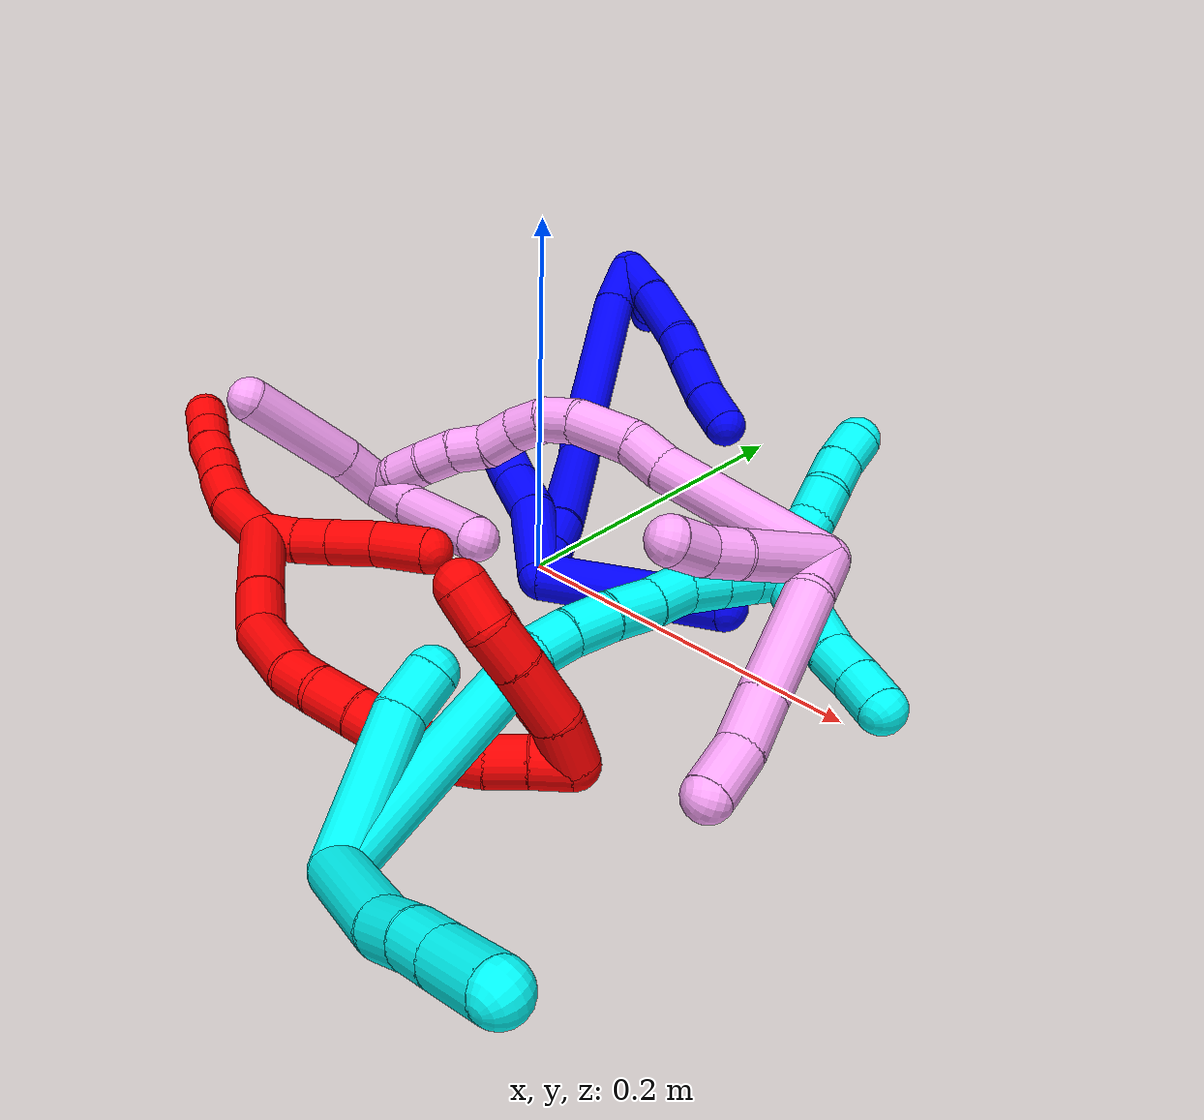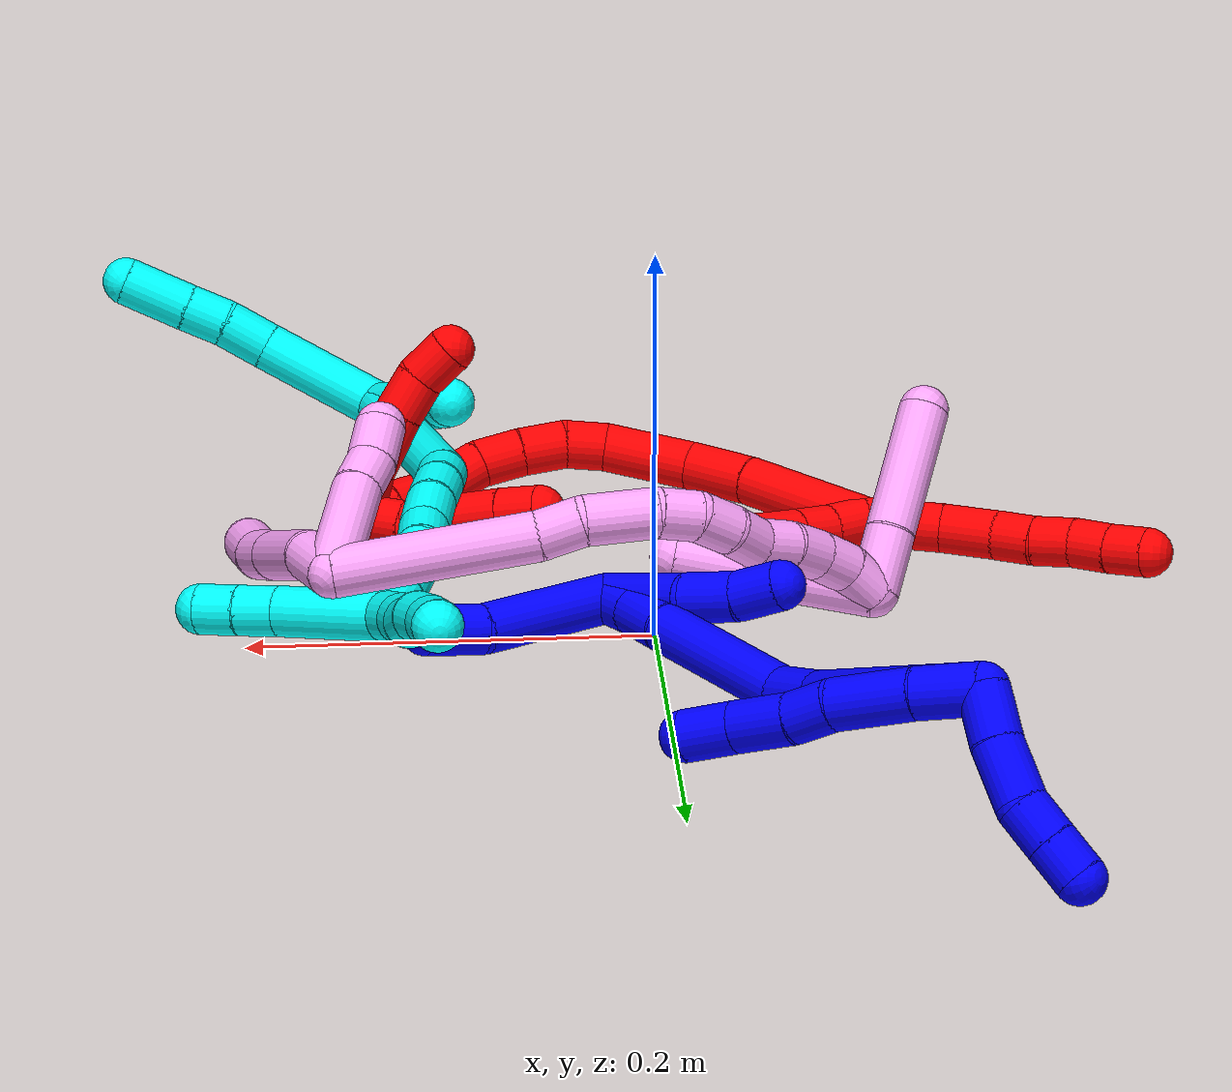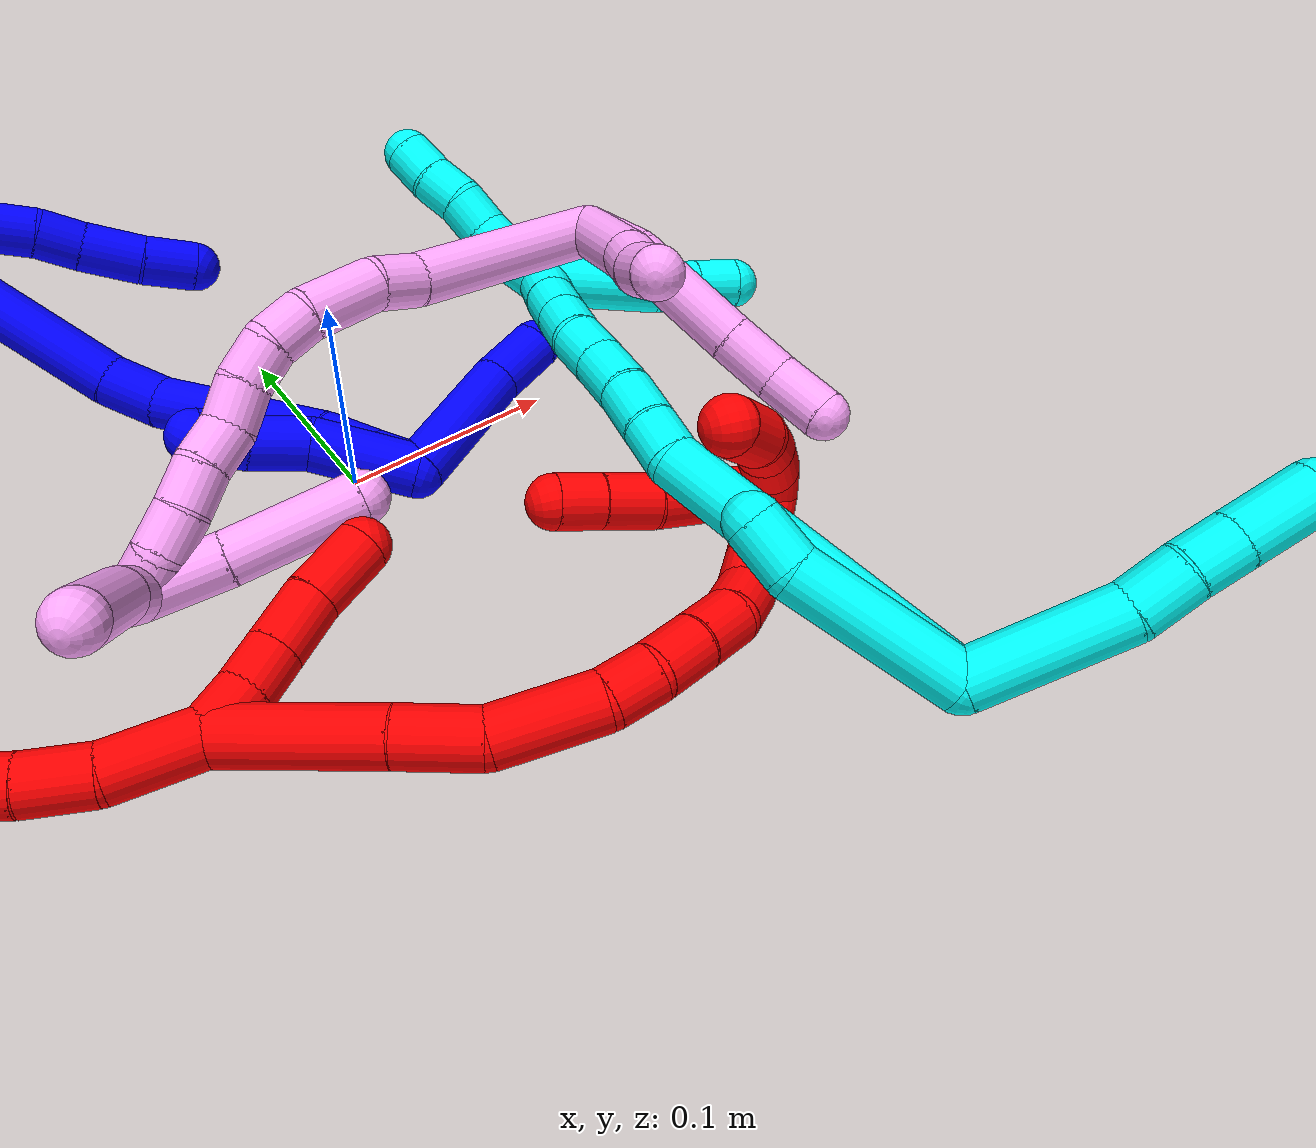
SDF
<sdf version="1.7">
 <world name="default">
  <plugin name="TubeGeneratorPlugin" filename="libtube_generator_plugin.so"/>
  <model name="photoneo_s_sensor">
   <static>1</static>
   <pose>0 0 2 1.57079 1.57079 3.14159</pose>
   <link name="link">
    <inertial><mass>0.1</mass></inertial>
    <sensor name="sensor" type="depth">
     <update_rate>30</update_rate>
     <camera>
      <horizontal_fov>1.22</horizontal_fov>
      <image><width>1920</width><height>1200</height><format>B8G8R8</format></image>
      <clip><near>0.1</near><far>4</far></clip>
      <depth_camera><output>points</output></depth_camera>
     </camera>
     <plugin name="camera_plugin" filename="libgazebo_ros_depth_camera.so">
      <baseline>0.2</baseline>
      <alwaysOn>1</alwaysOn>
      <updateRate>0.0</updateRate>
      <cameraName>camera_ir</cameraName>
      <imageTopicName>/camera/color/image_raw</imageTopicName>
      <cameraInfoTopicName>/camera/color/camera_info</cameraInfoTopicName>
      <depthImageTopicName>/camera/depth/image_raw</depthImageTopicName>
      <depthImageCameraInfoTopicName>/camera/depth/camera_info</depthImageCameraInfoTopicName>
      <pointCloudTopicName>/camera/depth/points</pointCloudTopicName>
      <frameName>fr_optical</frameName>
      <pointCloudCutoff>0.1</pointCloudCutoff>
      <pointCloudCutoffMax>2.0</pointCloudCutoffMax>
      <distortionK1>0</distortionK1>
      <distortionK2>0</distortionK2>
      <distortionK3>0</distortionK3>
      <distortionT1>0</distortionT1>
      <distortionT2>0</distortionT2>
      <CxPrime>0</CxPrime>
      <Cx>0</Cx>
      <Cy>0</Cy>
      <focalLength>0</focalLength>
      <hackBaseline>0</hackBaseline>
     </plugin>
    </sensor>
   </link>
  </model>
  <gravity>0 0 -9.8</gravity>
  <magnetic_field>6e-06 2.3e-05 -4.2e-05</magnetic_field>
  <atmosphere type="adiabatic"/>
  <physics name="default_physics" default="0" type="ode">
   <max_step_size>0.003</max_step_size>
   <real_time_factor>1</real_time_factor>
   <real_time_update_rate>1000</real_time_update_rate>
   <max_contacts>10000</max_contacts>
   <ode>
    <solver>
     <type>quick</type>
     <iters>100</iters>
     <sor>1.3</sor>
     <use_dynamic_moi_rescaling>0</use_dynamic_moi_rescaling>
    </solver>
    <constraints>
     <contact_max_correcting_vel>0</contact_max_correcting_vel>
     <contact_surface_layer>0.001</contact_surface_layer>
     <cfm>0</cfm>
     <erp>0.2</erp>
    </constraints>
   </ode>
  </physics>
  <scene><ambient>0.4 0.4 0.4 1</ambient><background>0.7 0.7 0.7 1</background><shadows>0</shadows></scene>
  <audio><device>default</device></audio>
  <spherical_coordinates>
   <surface_model>EARTH_WGS84</surface_model>
   <latitude_deg>0</latitude_deg>
   <longitude_deg>0</longitude_deg>
   <elevation>0</elevation>
   <heading_deg>0</heading_deg>
  </spherical_coordinates>
  <model name="bin">
   <static>1</static>
   <link name="bottom">
    <collision name="collision-bottom">
     <pose>0 0 -0.01 0 -0 0</pose>
     <geometry><box><size>0.8 0.6 0.02</size></box></geometry>
     <surface>
      <friction><ode><mu>100</mu><mu2>100</mu2></ode></friction>
      <contact><collide_bitmask>65535</collide_bitmask></contact>
     </surface>
    </collision>
   </link>
   <link name="west_wall">
    <collision name="collision-west_wall">
     <pose>-0.41 0 0.1 0 -0 0</pose>
     <geometry><box><size>0.02 0.6 0.2</size></box></geometry>
     <surface>
      <friction><ode><mu>100</mu><mu2>100</mu2></ode></friction>
      <contact><collide_bitmask>65535</collide_bitmask></contact>
     </surface>
    </collision>
   </link>
   <link name="east_wall">
    <collision name="collision-east_wall">
     <pose>0.41 0 0.1 0 -0 0</pose>
     <geometry><box><size>0.02 0.6 0.2</size></box></geometry>
     <surface>
      <friction><ode><mu>100</mu><mu2>100</mu2></ode></friction>
      <contact><collide_bitmask>65535</collide_bitmask></contact>
     </surface>
    </collision>
   </link>
   <link name="south_wall">
    <collision name="collision-south_wall">
     <pose>0 -0.31 0.1 0 -0 0</pose>
     <geometry><box><size>0.8 0.02 0.2</size></box></geometry>
     <surface>
      <friction><ode><mu>100</mu><mu2>100</mu2></ode></friction>
      <contact><collide_bitmask>65535</collide_bitmask></contact>
     </surface>
    </collision>
   </link>
   <link name="north_wall">
    <collision name="collision-north_wall">
     <pose>0 0.31 0.1 0 -0 0</pose>
     <geometry><box><size>0.8 0.02 0.2</size></box></geometry>
     <surface>
      <friction><ode><mu>100</mu><mu2>100</mu2></ode></friction>
      <contact><collide_bitmask>65535</collide_bitmask></contact>
     </surface>
    </collision>
   </link>
  </model>
  <model name="1">
   <static>0</static>
   <link name="1">
    <collision name="collision-cylinder-e_1_2_8">
     <pose>0.006815 7e-05 -0.014441 -3.13671 0.440934 -3.11982</pose>
     <geometry><cylinder><radius>0.0125</radius><length>0.031937</length></cylinder></geometry>
     <surface>
      <friction><ode><mu>1.16</mu><mu2>1.16</mu2><slip1>0</slip1><slip2>0</slip2></ode></friction>
      <contact><ode><kp>1e+06</kp><kd>1</kd><max_vel>0</max_vel><min_depth>0.001</min_depth></ode></contact>
     </surface>
    </collision>
    <visual name="visual-cylinder-e_1_2_8">
     <pose>0.006815 7e-05 -0.014441 -3.13671 0.440934 -3.11982</pose>
     <geometry><cylinder><radius>0.0125</radius><length>0.031937</length></cylinder></geometry>
     <material><ambient>0 0 1 1</ambient></material>
    </visual>
    <collision name="collision-cylinder-e_2_8_9">
     <pose>0.020682 0.001357 -0.047764 -3.07727 0.356748 -2.7884</pose>
     <geometry><cylinder><radius>0.0125</radius><length>0.040386</length></cylinder></geometry>
     <surface>
      <friction><ode><mu>1.16</mu><mu2>1.16</mu2><slip1>0</slip1><slip2>0</slip2></ode></friction>
      <contact><ode><kp>1e+06</kp><kd>1</kd><max_vel>0</max_vel><min_depth>0.001</min_depth></ode></contact>
     </surface>
    </collision>
    <visual name="visual-cylinder-e_2_8_9">
     <pose>0.020682 0.001357 -0.047764 -3.07727 0.356748 -2.7884</pose>
     <geometry><cylinder><radius>0.0125</radius><length>0.040386</length></cylinder></geometry>
     <material><ambient>0 0 1 1</ambient></material>
    </visual>
    <collision name="collision-cylinder-e_3_9_10">
     <pose>0.030269 0.004934 -0.076954 -2.91652 0.235266 -1.61546</pose>
     <geometry><cylinder><radius>0.0125</radius><length>0.021748</length></cylinder></geometry>
     <surface>
      <friction><ode><mu>1.16</mu><mu2>1.16</mu2><slip1>0</slip1><slip2>0</slip2></ode></friction>
      <contact><ode><kp>1e+06</kp><kd>1</kd><max_vel>0</max_vel><min_depth>0.001</min_depth></ode></contact>
     </surface>
    </collision>
    <visual name="visual-cylinder-e_3_9_10">
     <pose>0.030269 0.004934 -0.076954 -2.91652 0.235266 -1.61546</pose>
     <geometry><cylinder><radius>0.0125</radius><length>0.021748</length></cylinder></geometry>
     <material><ambient>0 0 1 1</ambient></material>
    </visual>
    <collision name="collision-cylinder-e_4_10_11">
     <pose>0.036464 0.008265 -0.101831 -3.07503 0.245622 -2.61465</pose>
     <geometry><cylinder><radius>0.0125</radius><length>0.030105</length></cylinder></geometry>
     <surface>
      <friction><ode><mu>1.16</mu><mu2>1.16</mu2><slip1>0</slip1><slip2>0</slip2></ode></friction>
      <contact><ode><kp>1e+06</kp><kd>1</kd><max_vel>0</max_vel><min_depth>0.001</min_depth></ode></contact>
     </surface>
    </collision>
    <visual name="visual-cylinder-e_4_10_11">
     <pose>0.036464 0.008265 -0.101831 -3.07503 0.245622 -2.61465</pose>
     <geometry><cylinder><radius>0.0125</radius><length>0.030105</length></cylinder></geometry>
     <material><ambient>0 0 1 1</ambient></material>
    </visual>
    <collision name="collision-cylinder-e_5_11_6">
     <pose>0.044853 0.010505 -0.128347 -3.03574 0.374986 -2.59703</pose>
     <geometry><cylinder><radius>0.0125</radius><length>0.025824</length></cylinder></geometry>
     <surface>
      <friction><ode><mu>1.16</mu><mu2>1.16</mu2><slip1>0</slip1><slip2>0</slip2></ode></friction>
      <contact><ode><kp>1e+06</kp><kd>1</kd><max_vel>0</max_vel><min_depth>0.001</min_depth></ode></contact>
     </surface>
    </collision>
    <visual name="visual-cylinder-e_5_11_6">
     <pose>0.044853 0.010505 -0.128347 -3.03574 0.374986 -2.59703</pose>
     <geometry><cylinder><radius>0.0125</radius><length>0.025824</length></cylinder></geometry>
     <material><ambient>0 0 1 1</ambient></material>
    </visual>
    <collision name="collision-cylinder-e_1_2_12">
     <pose>0.001063 0.01282 0.004372 -1.2421 0.078326 -0.056056</pose>
     <geometry><cylinder><radius>0.0125</radius><length>0.027174</length></cylinder></geometry>
     <surface>
      <friction><ode><mu>1.16</mu><mu2>1.16</mu2><slip1>0</slip1><slip2>0</slip2></ode></friction>
      <contact><ode><kp>1e+06</kp><kd>1</kd><max_vel>0</max_vel><min_depth>0.001</min_depth></ode></contact>
     </surface>
    </collision>
    <visual name="visual-cylinder-e_1_2_12">
     <pose>0.001063 0.01282 0.004372 -1.2421 0.078326 -0.056056</pose>
     <geometry><cylinder><radius>0.0125</radius><length>0.027174</length></cylinder></geometry>
     <material><ambient>0 0 1 1</ambient></material>
    </visual>
    <collision name="collision-cylinder-e_2_12_13">
     <pose>0.002004 0.039706 0.015026 -1.15079 -0.007917 0.005135</pose>
     <geometry><cylinder><radius>0.0125</radius><length>0.03081</length></cylinder></geometry>
     <surface>
      <friction><ode><mu>1.16</mu><mu2>1.16</mu2><slip1>0</slip1><slip2>0</slip2></ode></friction>
      <contact><ode><kp>1e+06</kp><kd>1</kd><max_vel>0</max_vel><min_depth>0.001</min_depth></ode></contact>
     </surface>
    </collision>
    <visual name="visual-cylinder-e_2_12_13">
     <pose>0.002004 0.039706 0.015026 -1.15079 -0.007917 0.005135</pose>
     <geometry><cylinder><radius>0.0125</radius><length>0.03081</length></cylinder></geometry>
     <material><ambient>0 0 1 1</ambient></material>
    </visual>
    <collision name="collision-cylinder-e_3_13_14">
     <pose>-0.001006 0.062426 0.026963 -0.992019 -0.272428 0.148067</pose>
     <geometry><cylinder><radius>0.0125</radius><length>0.021468</length></cylinder></geometry>
     <surface>
      <friction><ode><mu>1.16</mu><mu2>1.16</mu2><slip1>0</slip1><slip2>0</slip2></ode></friction>
      <contact><ode><kp>1e+06</kp><kd>1</kd><max_vel>0</max_vel><min_depth>0.001</min_depth></ode></contact>
     </surface>
    </collision>
    <visual name="visual-cylinder-e_3_13_14">
     <pose>-0.001006 0.062426 0.026963 -0.992019 -0.272428 0.148067</pose>
     <geometry><cylinder><radius>0.0125</radius><length>0.021468</length></cylinder></geometry>
     <material><ambient>0 0 1 1</ambient></material>
    </visual>
    <collision name="collision-cylinder-e_4_14_5">
     <pose>-0.006786 0.079346 0.037992 -0.994302 -0.285288 0.155544</pose>
     <geometry><cylinder><radius>0.0125</radius><length>0.020548</length></cylinder></geometry>
     <surface>
      <friction><ode><mu>1.16</mu><mu2>1.16</mu2><slip1>0</slip1><slip2>0</slip2></ode></friction>
      <contact><ode><kp>1e+06</kp><kd>1</kd><max_vel>0</max_vel><min_depth>0.001</min_depth></ode></contact>
     </surface>
    </collision>
    <visual name="visual-cylinder-e_4_14_5">
     <pose>-0.006786 0.079346 0.037992 -0.994302 -0.285288 0.155544</pose>
     <geometry><cylinder><radius>0.0125</radius><length>0.020548</length></cylinder></geometry>
     <material><ambient>0 0 1 1</ambient></material>
    </visual>
    <collision name="collision-cylinder-e_1_2_15">
     <pose>-0.005805 -0.000931 -0.015453 3.08144 -0.358739 -2.81272</pose>
     <geometry><cylinder><radius>0.0125</radius><length>0.033067</length></cylinder></geometry>
     <surface>
      <friction><ode><mu>1.16</mu><mu2>1.16</mu2><slip1>0</slip1><slip2>0</slip2></ode></friction>
      <contact><ode><kp>1e+06</kp><kd>1</kd><max_vel>0</max_vel><min_depth>0.001</min_depth></ode></contact>
     </surface>
    </collision>
    <visual name="visual-cylinder-e_1_2_15">
     <pose>-0.005805 -0.000931 -0.015453 3.08144 -0.358739 -2.81272</pose>
     <geometry><cylinder><radius>0.0125</radius><length>0.033067</length></cylinder></geometry>
     <material><ambient>0 0 1 1</ambient></material>
    </visual>
    <collision name="collision-cylinder-e_2_15_16">
     <pose>-0.02283 -0.004625 -0.082101 3.08767 -0.215453 -2.65285</pose>
     <geometry><cylinder><radius>0.0125</radius><length>0.104966</length></cylinder></geometry>
     <surface>
      <friction><ode><mu>1.16</mu><mu2>1.16</mu2><slip1>0</slip1><slip2>0</slip2></ode></friction>
      <contact><ode><kp>1e+06</kp><kd>1</kd><max_vel>0</max_vel><min_depth>0.001</min_depth></ode></contact>
     </surface>
    </collision>
    <visual name="visual-cylinder-e_2_15_16">
     <pose>-0.02283 -0.004625 -0.082101 3.08767 -0.215453 -2.65285</pose>
     <geometry><cylinder><radius>0.0125</radius><length>0.104966</length></cylinder></geometry>
     <material><ambient>0 0 1 1</ambient></material>
    </visual>
    <collision name="collision-cylinder-e_3_16_17">
     <pose>-0.035182 -0.009597 -0.146752 2.97887 -0.082822 -0.940277</pose>
     <geometry><cylinder><radius>0.0125</radius><length>0.027365</length></cylinder></geometry>
     <surface>
      <friction><ode><mu>1.16</mu><mu2>1.16</mu2><slip1>0</slip1><slip2>0</slip2></ode></friction>
      <contact><ode><kp>1e+06</kp><kd>1</kd><max_vel>0</max_vel><min_depth>0.001</min_depth></ode></contact>
     </surface>
    </collision>
    <visual name="visual-cylinder-e_3_16_17">
     <pose>-0.035182 -0.009597 -0.146752 2.97887 -0.082822 -0.940277</pose>
     <geometry><cylinder><radius>0.0125</radius><length>0.027365</length></cylinder></geometry>
     <material><ambient>0 0 1 1</ambient></material>
    </visual>
    <collision name="collision-cylinder-e_4_17_18">
     <pose>-0.036718 -0.030428 -0.198703 2.69102 -0.009438 -0.041179</pose>
     <geometry><cylinder><radius>0.0125</radius><length>0.085532</length></cylinder></geometry>
     <surface>
      <friction><ode><mu>1.16</mu><mu2>1.16</mu2><slip1>0</slip1><slip2>0</slip2></ode></friction>
      <contact><ode><kp>1e+06</kp><kd>1</kd><max_vel>0</max_vel><min_depth>0.001</min_depth></ode></contact>
     </surface>
    </collision>
    <visual name="visual-cylinder-e_4_17_18">
     <pose>-0.036718 -0.030428 -0.198703 2.69102 -0.009438 -0.041179</pose>
     <geometry><cylinder><radius>0.0125</radius><length>0.085532</length></cylinder></geometry>
     <material><ambient>0 0 1 1</ambient></material>
    </visual>
    <collision name="collision-cylinder-e_5_18_19">
     <pose>-0.038938 -0.054391 -0.249311 2.7263 -0.136372 -0.626926</pose>
     <geometry><cylinder><radius>0.0125</radius><length>0.026721</length></cylinder></geometry>
     <surface>
      <friction><ode><mu>1.16</mu><mu2>1.16</mu2><slip1>0</slip1><slip2>0</slip2></ode></friction>
      <contact><ode><kp>1e+06</kp><kd>1</kd><max_vel>0</max_vel><min_depth>0.001</min_depth></ode></contact>
     </surface>
    </collision>
    <visual name="visual-cylinder-e_5_18_19">
     <pose>-0.038938 -0.054391 -0.249311 2.7263 -0.136372 -0.626926</pose>
     <geometry><cylinder><radius>0.0125</radius><length>0.026721</length></cylinder></geometry>
     <material><ambient>0 0 1 1</ambient></material>
    </visual>
    <collision name="collision-cylinder-e_6_19_1">
     <pose>-0.041743 -0.063685 -0.271827 2.77853 -0.088566 -0.473758</pose>
     <geometry><cylinder><radius>0.0125</radius><length>0.022349</length></cylinder></geometry>
     <surface>
      <friction><ode><mu>1.16</mu><mu2>1.16</mu2><slip1>0</slip1><slip2>0</slip2></ode></friction>
      <contact><ode><kp>1e+06</kp><kd>1</kd><max_vel>0</max_vel><min_depth>0.001</min_depth></ode></contact>
     </surface>
    </collision>
    <visual name="visual-cylinder-e_6_19_1">
     <pose>-0.041743 -0.063685 -0.271827 2.77853 -0.088566 -0.473758</pose>
     <geometry><cylinder><radius>0.0125</radius><length>0.022349</length></cylinder></geometry>
     <material><ambient>0 0 1 1</ambient></material>
    </visual>
    <collision name="collision-cylinder-e_1_1_20">
     <pose>-0.045527 -0.065529 -0.257876 -0.086354 -0.113898 0.004926</pose>
     <geometry><cylinder><radius>0.0125</radius><length>0.049213</length></cylinder></geometry>
     <surface>
      <friction><ode><mu>1.16</mu><mu2>1.16</mu2><slip1>0</slip1><slip2>0</slip2></ode></friction>
      <contact><ode><kp>1e+06</kp><kd>1</kd><max_vel>0</max_vel><min_depth>0.001</min_depth></ode></contact>
     </surface>
    </collision>
    <visual name="visual-cylinder-e_1_1_20">
     <pose>-0.045527 -0.065529 -0.257876 -0.086354 -0.113898 0.004926</pose>
     <geometry><cylinder><radius>0.0125</radius><length>0.049213</length></cylinder></geometry>
     <material><ambient>0 0 1 1</ambient></material>
    </visual>
    <collision name="collision-cylinder-e_2_20_21">
     <pose>-0.053507 -0.0628 -0.22091 -0.049154 -0.389509 0.009698</pose>
     <geometry><cylinder><radius>0.0125</radius><length>0.027296</length></cylinder></geometry>
     <surface>
      <friction><ode><mu>1.16</mu><mu2>1.16</mu2><slip1>0</slip1><slip2>0</slip2></ode></friction>
      <contact><ode><kp>1e+06</kp><kd>1</kd><max_vel>0</max_vel><min_depth>0.001</min_depth></ode></contact>
     </surface>
    </collision>
    <visual name="visual-cylinder-e_2_20_21">
     <pose>-0.053507 -0.0628 -0.22091 -0.049154 -0.389509 0.009698</pose>
     <geometry><cylinder><radius>0.0125</radius><length>0.027296</length></cylinder></geometry>
     <material><ambient>0 0 1 1</ambient></material>
    </visual>
    <collision name="collision-cylinder-e_3_21_4">
     <pose>-0.062646 -0.064009 -0.197393 0.166172 -0.343572 -0.028895</pose>
     <geometry><cylinder><radius>0.0125</radius><length>0.023491</length></cylinder></geometry>
     <surface>
      <friction><ode><mu>1.16</mu><mu2>1.16</mu2><slip1>0</slip1><slip2>0</slip2></ode></friction>
      <contact><ode><kp>1e+06</kp><kd>1</kd><max_vel>0</max_vel><min_depth>0.001</min_depth></ode></contact>
     </surface>
    </collision>
    <visual name="visual-cylinder-e_3_21_4">
     <pose>-0.062646 -0.064009 -0.197393 0.166172 -0.343572 -0.028895</pose>
     <geometry><cylinder><radius>0.0125</radius><length>0.023491</length></cylinder></geometry>
     <material><ambient>0 0 1 1</ambient></material>
    </visual>
    <collision name="collision-cylinder-e_1_1_22">
     <pose>-0.00985 -0.059947 -0.292113 -2.48018 1.20696 -2.21735</pose>
     <geometry><cylinder><radius>0.0125</radius><length>0.070368</length></cylinder></geometry>
     <surface>
      <friction><ode><mu>1.16</mu><mu2>1.16</mu2><slip1>0</slip1><slip2>0</slip2></ode></friction>
      <contact><ode><kp>1e+06</kp><kd>1</kd><max_vel>0</max_vel><min_depth>0.001</min_depth></ode></contact>
     </surface>
    </collision>
    <visual name="visual-cylinder-e_1_1_22">
     <pose>-0.00985 -0.059947 -0.292113 -2.48018 1.20696 -2.21735</pose>
     <geometry><cylinder><radius>0.0125</radius><length>0.070368</length></cylinder></geometry>
     <material><ambient>0 0 1 1</ambient></material>
    </visual>
    <collision name="collision-cylinder-e_2_22_3">
     <pose>0.036567 -0.052107 -0.308016 -3.11668 1.15202 -3.10324</pose>
     <geometry><cylinder><radius>0.0125</radius><length>0.029632</length></cylinder></geometry>
     <surface>
      <friction><ode><mu>1.16</mu><mu2>1.16</mu2><slip1>0</slip1><slip2>0</slip2></ode></friction>
      <contact><ode><kp>1e+06</kp><kd>1</kd><max_vel>0</max_vel><min_depth>0.001</min_depth></ode></contact>
     </surface>
    </collision>
    <visual name="visual-cylinder-e_2_22_3">
     <pose>0.036567 -0.052107 -0.308016 -3.11668 1.15202 -3.10324</pose>
     <geometry><cylinder><radius>0.0125</radius><length>0.029632</length></cylinder></geometry>
     <material><ambient>0 0 1 1</ambient></material>
    </visual>
    <collision name="collision-sphere-3">
     <pose>0.050102 -0.051957 -0.314039 0 -0 0</pose>
     <geometry><sphere><radius>0.0125</radius></sphere></geometry>
     <surface>
      <friction><ode><mu>1.16</mu><mu2>1.16</mu2><slip1>0</slip1><slip2>0</slip2></ode></friction>
      <contact><ode><kp>1e+06</kp><kd>1</kd><max_vel>0</max_vel><min_depth>0.001</min_depth></ode></contact>
     </surface>
    </collision>
    <visual name="visual-sphere-3">
     <pose>0.050102 -0.051957 -0.314039 0 -0 0</pose>
     <geometry><sphere><radius>0.0125</radius></sphere></geometry>
     <material><ambient>0 0 1 1</ambient></material>
    </visual>
    <collision name="collision-sphere-22">
     <pose>0.023031 -0.052257 -0.301993 0 -0 0</pose>
     <geometry><sphere><radius>0.0125</radius></sphere></geometry>
     <surface>
      <friction><ode><mu>1.16</mu><mu2>1.16</mu2><slip1>0</slip1><slip2>0</slip2></ode></friction>
      <contact><ode><kp>1e+06</kp><kd>1</kd><max_vel>0</max_vel><min_depth>0.001</min_depth></ode></contact>
     </surface>
    </collision>
    <visual name="visual-sphere-22">
     <pose>0.023031 -0.052257 -0.301993 0 -0 0</pose>
     <geometry><sphere><radius>0.0125</radius></sphere></geometry>
     <material><ambient>0 0 1 1</ambient></material>
    </visual>
    <collision name="collision-sphere-4">
     <pose>-0.066602 -0.065839 -0.186486 0 -0 0</pose>
     <geometry><sphere><radius>0.0125</radius></sphere></geometry>
     <surface>
      <friction><ode><mu>1.16</mu><mu2>1.16</mu2><slip1>0</slip1><slip2>0</slip2></ode></friction>
      <contact><ode><kp>1e+06</kp><kd>1</kd><max_vel>0</max_vel><min_depth>0.001</min_depth></ode></contact>
     </surface>
    </collision>
    <visual name="visual-sphere-4">
     <pose>-0.066602 -0.065839 -0.186486 0 -0 0</pose>
     <geometry><sphere><radius>0.0125</radius></sphere></geometry>
     <material><ambient>0 0 1 1</ambient></material>
    </visual>
    <collision name="collision-sphere-21">
     <pose>-0.058689 -0.06218 -0.2083 0 -0 0</pose>
     <geometry><sphere><radius>0.0125</radius></sphere></geometry>
     <surface>
      <friction><ode><mu>1.16</mu><mu2>1.16</mu2><slip1>0</slip1><slip2>0</slip2></ode></friction>
      <contact><ode><kp>1e+06</kp><kd>1</kd><max_vel>0</max_vel><min_depth>0.001</min_depth></ode></contact>
     </surface>
    </collision>
    <visual name="visual-sphere-21">
     <pose>-0.058689 -0.06218 -0.2083 0 -0 0</pose>
     <geometry><sphere><radius>0.0125</radius></sphere></geometry>
     <material><ambient>0 0 1 1</ambient></material>
    </visual>
    <collision name="collision-sphere-20">
     <pose>-0.048324 -0.063421 -0.233521 0 -0 0</pose>
     <geometry><sphere><radius>0.0125</radius></sphere></geometry>
     <surface>
      <friction><ode><mu>1.16</mu><mu2>1.16</mu2><slip1>0</slip1><slip2>0</slip2></ode></friction>
      <contact><ode><kp>1e+06</kp><kd>1</kd><max_vel>0</max_vel><min_depth>0.001</min_depth></ode></contact>
     </surface>
    </collision>
    <visual name="visual-sphere-20">
     <pose>-0.048324 -0.063421 -0.233521 0 -0 0</pose>
     <geometry><sphere><radius>0.0125</radius></sphere></geometry>
     <material><ambient>0 0 1 1</ambient></material>
    </visual>
    <collision name="collision-sphere-6">
     <pose>0.049582 0.011775 -0.140294 0 -0 0</pose>
     <geometry><sphere><radius>0.0125</radius></sphere></geometry>
     <surface>
      <friction><ode><mu>1.16</mu><mu2>1.16</mu2><slip1>0</slip1><slip2>0</slip2></ode></friction>
      <contact><ode><kp>1e+06</kp><kd>1</kd><max_vel>0</max_vel><min_depth>0.001</min_depth></ode></contact>
     </surface>
    </collision>
    <visual name="visual-sphere-6">
     <pose>0.049582 0.011775 -0.140294 0 -0 0</pose>
     <geometry><sphere><radius>0.0125</radius></sphere></geometry>
     <material><ambient>0 0 1 1</ambient></material>
    </visual>
    <collision name="collision-sphere-11">
     <pose>0.040124 0.009236 -0.116399 0 -0 0</pose>
     <geometry><sphere><radius>0.0125</radius></sphere></geometry>
     <surface>
      <friction><ode><mu>1.16</mu><mu2>1.16</mu2><slip1>0</slip1><slip2>0</slip2></ode></friction>
      <contact><ode><kp>1e+06</kp><kd>1</kd><max_vel>0</max_vel><min_depth>0.001</min_depth></ode></contact>
     </surface>
    </collision>
    <visual name="visual-sphere-11">
     <pose>0.040124 0.009236 -0.116399 0 -0 0</pose>
     <geometry><sphere><radius>0.0125</radius></sphere></geometry>
     <material><ambient>0 0 1 1</ambient></material>
    </visual>
    <collision name="collision-sphere-10">
     <pose>0.032804 0.007294 -0.087262 0 -0 0</pose>
     <geometry><sphere><radius>0.0125</radius></sphere></geometry>
     <surface>
      <friction><ode><mu>1.16</mu><mu2>1.16</mu2><slip1>0</slip1><slip2>0</slip2></ode></friction>
      <contact><ode><kp>1e+06</kp><kd>1</kd><max_vel>0</max_vel><min_depth>0.001</min_depth></ode></contact>
     </surface>
    </collision>
    <visual name="visual-sphere-10">
     <pose>0.032804 0.007294 -0.087262 0 -0 0</pose>
     <geometry><sphere><radius>0.0125</radius></sphere></geometry>
     <material><ambient>0 0 1 1</ambient></material>
    </visual>
    <collision name="collision-sphere-9">
     <pose>0.027734 0.002573 -0.066647 0 -0 0</pose>
     <geometry><sphere><radius>0.0125</radius></sphere></geometry>
     <surface>
      <friction><ode><mu>1.16</mu><mu2>1.16</mu2><slip1>0</slip1><slip2>0</slip2></ode></friction>
      <contact><ode><kp>1e+06</kp><kd>1</kd><max_vel>0</max_vel><min_depth>0.001</min_depth></ode></contact>
     </surface>
    </collision>
    <visual name="visual-sphere-9">
     <pose>0.027734 0.002573 -0.066647 0 -0 0</pose>
     <geometry><sphere><radius>0.0125</radius></sphere></geometry>
     <material><ambient>0 0 1 1</ambient></material>
    </visual>
    <collision name="collision-sphere-2">
     <geometry><sphere><radius>0.0125</radius></sphere></geometry>
     <surface>
      <friction><ode><mu>1.16</mu><mu2>1.16</mu2><slip1>0</slip1><slip2>0</slip2></ode></friction>
      <contact><ode><kp>1e+06</kp><kd>1</kd><max_vel>0</max_vel><min_depth>0.001</min_depth></ode></contact>
     </surface>
    </collision>
    <visual name="visual-sphere-2">
     <geometry><sphere><radius>0.0125</radius></sphere></geometry>
     <material><ambient>0 0 1 1</ambient></material>
    </visual>
    <collision name="collision-sphere-19">
     <pose>-0.040754 -0.059732 -0.261422 0 -0 0</pose>
     <geometry><sphere><radius>0.0125</radius></sphere></geometry>
     <surface>
      <friction><ode><mu>1.16</mu><mu2>1.16</mu2><slip1>0</slip1><slip2>0</slip2></ode></friction>
      <contact><ode><kp>1e+06</kp><kd>1</kd><max_vel>0</max_vel><min_depth>0.001</min_depth></ode></contact>
     </surface>
    </collision>
    <visual name="visual-sphere-19">
     <pose>-0.040754 -0.059732 -0.261422 0 -0 0</pose>
     <geometry><sphere><radius>0.0125</radius></sphere></geometry>
     <material><ambient>0 0 1 1</ambient></material>
    </visual>
    <collision name="collision-sphere-8">
     <pose>0.01363 0.000141 -0.028882 0 -0 0</pose>
     <geometry><sphere><radius>0.0125</radius></sphere></geometry>
     <surface>
      <friction><ode><mu>1.16</mu><mu2>1.16</mu2><slip1>0</slip1><slip2>0</slip2></ode></friction>
      <contact><ode><kp>1e+06</kp><kd>1</kd><max_vel>0</max_vel><min_depth>0.001</min_depth></ode></contact>
     </surface>
    </collision>
    <visual name="visual-sphere-8">
     <pose>0.01363 0.000141 -0.028882 0 -0 0</pose>
     <geometry><sphere><radius>0.0125</radius></sphere></geometry>
     <material><ambient>0 0 1 1</ambient></material>
    </visual>
    <collision name="collision-sphere-12">
     <pose>0.002126 0.02564 0.008745 0 -0 0</pose>
     <geometry><sphere><radius>0.0125</radius></sphere></geometry>
     <surface>
      <friction><ode><mu>1.16</mu><mu2>1.16</mu2><slip1>0</slip1><slip2>0</slip2></ode></friction>
      <contact><ode><kp>1e+06</kp><kd>1</kd><max_vel>0</max_vel><min_depth>0.001</min_depth></ode></contact>
     </surface>
    </collision>
    <visual name="visual-sphere-12">
     <pose>0.002126 0.02564 0.008745 0 -0 0</pose>
     <geometry><sphere><radius>0.0125</radius></sphere></geometry>
     <material><ambient>0 0 1 1</ambient></material>
    </visual>
    <collision name="collision-sphere-13">
     <pose>0.001882 0.053771 0.021308 0 -0 0</pose>
     <geometry><sphere><radius>0.0125</radius></sphere></geometry>
     <surface>
      <friction><ode><mu>1.16</mu><mu2>1.16</mu2><slip1>0</slip1><slip2>0</slip2></ode></friction>
      <contact><ode><kp>1e+06</kp><kd>1</kd><max_vel>0</max_vel><min_depth>0.001</min_depth></ode></contact>
     </surface>
    </collision>
    <visual name="visual-sphere-13">
     <pose>0.001882 0.053771 0.021308 0 -0 0</pose>
     <geometry><sphere><radius>0.0125</radius></sphere></geometry>
     <material><ambient>0 0 1 1</ambient></material>
    </visual>
    <collision name="collision-sphere-14">
     <pose>-0.003894 0.07108 0.032618 0 -0 0</pose>
     <geometry><sphere><radius>0.0125</radius></sphere></geometry>
     <surface>
      <friction><ode><mu>1.16</mu><mu2>1.16</mu2><slip1>0</slip1><slip2>0</slip2></ode></friction>
      <contact><ode><kp>1e+06</kp><kd>1</kd><max_vel>0</max_vel><min_depth>0.001</min_depth></ode></contact>
     </surface>
    </collision>
    <visual name="visual-sphere-14">
     <pose>-0.003894 0.07108 0.032618 0 -0 0</pose>
     <geometry><sphere><radius>0.0125</radius></sphere></geometry>
     <material><ambient>0 0 1 1</ambient></material>
    </visual>
    <collision name="collision-sphere-5">
     <pose>-0.009677 0.087611 0.043366 0 -0 0</pose>
     <geometry><sphere><radius>0.0125</radius></sphere></geometry>
     <surface>
      <friction><ode><mu>1.16</mu><mu2>1.16</mu2><slip1>0</slip1><slip2>0</slip2></ode></friction>
      <contact><ode><kp>1e+06</kp><kd>1</kd><max_vel>0</max_vel><min_depth>0.001</min_depth></ode></contact>
     </surface>
    </collision>
    <visual name="visual-sphere-5">
     <pose>-0.009677 0.087611 0.043366 0 -0 0</pose>
     <geometry><sphere><radius>0.0125</radius></sphere></geometry>
     <material><ambient>0 0 1 1</ambient></material>
    </visual>
    <collision name="collision-sphere-15">
     <pose>-0.01161 -0.001861 -0.030906 0 -0 0</pose>
     <geometry><sphere><radius>0.0125</radius></sphere></geometry>
     <surface>
      <friction><ode><mu>1.16</mu><mu2>1.16</mu2><slip1>0</slip1><slip2>0</slip2></ode></friction>
      <contact><ode><kp>1e+06</kp><kd>1</kd><max_vel>0</max_vel><min_depth>0.001</min_depth></ode></contact>
     </surface>
    </collision>
    <visual name="visual-sphere-15">
     <pose>-0.01161 -0.001861 -0.030906 0 -0 0</pose>
     <geometry><sphere><radius>0.0125</radius></sphere></geometry>
     <material><ambient>0 0 1 1</ambient></material>
    </visual>
    <collision name="collision-sphere-16">
     <pose>-0.03405 -0.007388 -0.133296 0 -0 0</pose>
     <geometry><sphere><radius>0.0125</radius></sphere></geometry>
     <surface>
      <friction><ode><mu>1.16</mu><mu2>1.16</mu2><slip1>0</slip1><slip2>0</slip2></ode></friction>
      <contact><ode><kp>1e+06</kp><kd>1</kd><max_vel>0</max_vel><min_depth>0.001</min_depth></ode></contact>
     </surface>
    </collision>
    <visual name="visual-sphere-16">
     <pose>-0.03405 -0.007388 -0.133296 0 -0 0</pose>
     <geometry><sphere><radius>0.0125</radius></sphere></geometry>
     <material><ambient>0 0 1 1</ambient></material>
    </visual>
    <collision name="collision-sphere-17">
     <pose>-0.036314 -0.011806 -0.160207 0 -0 0</pose>
     <geometry><sphere><radius>0.0125</radius></sphere></geometry>
     <surface>
      <friction><ode><mu>1.16</mu><mu2>1.16</mu2><slip1>0</slip1><slip2>0</slip2></ode></friction>
      <contact><ode><kp>1e+06</kp><kd>1</kd><max_vel>0</max_vel><min_depth>0.001</min_depth></ode></contact>
     </surface>
    </collision>
    <visual name="visual-sphere-17">
     <pose>-0.036314 -0.011806 -0.160207 0 -0 0</pose>
     <geometry><sphere><radius>0.0125</radius></sphere></geometry>
     <material><ambient>0 0 1 1</ambient></material>
    </visual>
    <collision name="collision-sphere-18">
     <pose>-0.037121 -0.049051 -0.237199 0 -0 0</pose>
     <geometry><sphere><radius>0.0125</radius></sphere></geometry>
     <surface>
      <friction><ode><mu>1.16</mu><mu2>1.16</mu2><slip1>0</slip1><slip2>0</slip2></ode></friction>
      <contact><ode><kp>1e+06</kp><kd>1</kd><max_vel>0</max_vel><min_depth>0.001</min_depth></ode></contact>
     </surface>
    </collision>
    <visual name="visual-sphere-18">
     <pose>-0.037121 -0.049051 -0.237199 0 -0 0</pose>
     <geometry><sphere><radius>0.0125</radius></sphere></geometry>
     <material><ambient>0 0 1 1</ambient></material>
    </visual>
    <collision name="collision-sphere-1">
     <pose>-0.042731 -0.067638 -0.282232 0 -0 0</pose>
     <geometry><sphere><radius>0.0125</radius></sphere></geometry>
     <surface>
      <friction><ode><mu>1.16</mu><mu2>1.16</mu2><slip1>0</slip1><slip2>0</slip2></ode></friction>
      <contact><ode><kp>1e+06</kp><kd>1</kd><max_vel>0</max_vel><min_depth>0.001</min_depth></ode></contact>
     </surface>
    </collision>
    <visual name="visual-sphere-1">
     <pose>-0.042731 -0.067638 -0.282232 0 -0 0</pose>
     <geometry><sphere><radius>0.0125</radius></sphere></geometry>
     <material><ambient>0 0 1 1</ambient></material>
    </visual>
    <inertial>
     <pose>-0.012734 -0.017649 -0.139227 0 -0 0</pose>
     <mass>0.75</mass>
     <inertia>
      <ixx>-9.2e-05</ixx>
      <ixy>0</ixy>
      <ixz>0</ixz>
      <iyy>4.2e-05</iyy>
      <iyz>0</iyz>
      <izz>-2.1e-05</izz>
     </inertia>
    </inertial>
   </link>
   <pose>-0.131349 0.221623 0.074144 -1.15816 -0.326781 0.64767</pose>
  </model>
  <model name="2">
   <static>0</static>
   <link name="2">
    <collision name="collision-cylinder-e_1_2_8">
     <pose>0.0016 0.001524 -0.019834 -3.06493 0.080258 -1.61665</pose>
     <geometry><cylinder><radius>0.0125</radius><length>0.039914</length></cylinder></geometry>
     <surface>
      <friction><ode><mu>1.16</mu><mu2>1.16</mu2><slip1>0</slip1><slip2>0</slip2></ode></friction>
      <contact><ode><kp>1e+06</kp><kd>1</kd><max_vel>0</max_vel><min_depth>0.001</min_depth></ode></contact>
     </surface>
    </collision>
    <visual name="visual-cylinder-e_1_2_8">
     <pose>0.0016 0.001524 -0.019834 -3.06493 0.080258 -1.61665</pose>
     <geometry><cylinder><radius>0.0125</radius><length>0.039914</length></cylinder></geometry>
     <material><ambient>1 0 0 1</ambient></material>
    </visual>
    <collision name="collision-cylinder-e_2_8_9">
     <pose>0.001254 0.002547 -0.054053 3.10681 -0.134389 -2.63577</pose>
     <geometry><cylinder><radius>0.0125</radius><length>0.029049</length></cylinder></geometry>
     <surface>
      <friction><ode><mu>1.16</mu><mu2>1.16</mu2><slip1>0</slip1><slip2>0</slip2></ode></friction>
      <contact><ode><kp>1e+06</kp><kd>1</kd><max_vel>0</max_vel><min_depth>0.001</min_depth></ode></contact>
     </surface>
    </collision>
    <visual name="visual-cylinder-e_2_8_9">
     <pose>0.001254 0.002547 -0.054053 3.10681 -0.134389 -2.63577</pose>
     <geometry><cylinder><radius>0.0125</radius><length>0.029049</length></cylinder></geometry>
     <material><ambient>1 0 0 1</ambient></material>
    </visual>
    <collision name="collision-cylinder-e_3_9_10">
     <pose>-0.002859 0.001289 -0.078248 3.06459 -0.216809 -2.4612</pose>
     <geometry><cylinder><radius>0.0125</radius><length>0.02015</length></cylinder></geometry>
     <surface>
      <friction><ode><mu>1.16</mu><mu2>1.16</mu2><slip1>0</slip1><slip2>0</slip2></ode></friction>
      <contact><ode><kp>1e+06</kp><kd>1</kd><max_vel>0</max_vel><min_depth>0.001</min_depth></ode></contact>
     </surface>
    </collision>
    <visual name="visual-cylinder-e_3_9_10">
     <pose>-0.002859 0.001289 -0.078248 3.06459 -0.216809 -2.4612</pose>
     <geometry><cylinder><radius>0.0125</radius><length>0.02015</length></cylinder></geometry>
     <material><ambient>1 0 0 1</ambient></material>
    </visual>
    <collision name="collision-cylinder-e_4_10_11">
     <pose>-0.005943 -0.000512 -0.09838 3.04074 -0.088127 -1.43614</pose>
     <geometry><cylinder><radius>0.0125</radius><length>0.02083</length></cylinder></geometry>
     <surface>
      <friction><ode><mu>1.16</mu><mu2>1.16</mu2><slip1>0</slip1><slip2>0</slip2></ode></friction>
      <contact><ode><kp>1e+06</kp><kd>1</kd><max_vel>0</max_vel><min_depth>0.001</min_depth></ode></contact>
     </surface>
    </collision>
    <visual name="visual-cylinder-e_4_10_11">
     <pose>-0.005943 -0.000512 -0.09838 3.04074 -0.088127 -1.43614</pose>
     <geometry><cylinder><radius>0.0125</radius><length>0.02083</length></cylinder></geometry>
     <material><ambient>1 0 0 1</ambient></material>
    </visual>
    <collision name="collision-cylinder-e_5_11_12">
     <pose>-0.009537 -0.002526 -0.118313 3.04106 -0.270317 -2.43293</pose>
     <geometry><cylinder><radius>0.0125</radius><length>0.020047</length></cylinder></geometry>
     <surface>
      <friction><ode><mu>1.16</mu><mu2>1.16</mu2><slip1>0</slip1><slip2>0</slip2></ode></friction>
      <contact><ode><kp>1e+06</kp><kd>1</kd><max_vel>0</max_vel><min_depth>0.001</min_depth></ode></contact>
     </surface>
    </collision>
    <visual name="visual-cylinder-e_5_11_12">
     <pose>-0.009537 -0.002526 -0.118313 3.04106 -0.270317 -2.43293</pose>
     <geometry><cylinder><radius>0.0125</radius><length>0.020047</length></cylinder></geometry>
     <material><ambient>1 0 0 1</ambient></material>
    </visual>
    <collision name="collision-cylinder-e_6_12_6">
     <pose>-0.0145 -0.004906 -0.137561 2.99632 -0.230567 -2.01956</pose>
     <geometry><cylinder><radius>0.0125</radius><length>0.02001</length></cylinder></geometry>
     <surface>
      <friction><ode><mu>1.16</mu><mu2>1.16</mu2><slip1>0</slip1><slip2>0</slip2></ode></friction>
      <contact><ode><kp>1e+06</kp><kd>1</kd><max_vel>0</max_vel><min_depth>0.001</min_depth></ode></contact>
     </surface>
    </collision>
    <visual name="visual-cylinder-e_6_12_6">
     <pose>-0.0145 -0.004906 -0.137561 2.99632 -0.230567 -2.01956</pose>
     <geometry><cylinder><radius>0.0125</radius><length>0.02001</length></cylinder></geometry>
     <material><ambient>1 0 0 1</ambient></material>
    </visual>
    <collision name="collision-cylinder-e_1_2_13">
     <pose>-0.00728 -0.001985 0.00773 0.251372 -0.739488 -0.097862</pose>
     <geometry><cylinder><radius>0.0125</radius><length>0.021606</length></cylinder></geometry>
     <surface>
      <friction><ode><mu>1.16</mu><mu2>1.16</mu2><slip1>0</slip1><slip2>0</slip2></ode></friction>
      <contact><ode><kp>1e+06</kp><kd>1</kd><max_vel>0</max_vel><min_depth>0.001</min_depth></ode></contact>
     </surface>
    </collision>
    <visual name="visual-cylinder-e_1_2_13">
     <pose>-0.00728 -0.001985 0.00773 0.251372 -0.739488 -0.097862</pose>
     <geometry><cylinder><radius>0.0125</radius><length>0.021606</length></cylinder></geometry>
     <material><ambient>1 0 0 1</ambient></material>
    </visual>
    <collision name="collision-cylinder-e_2_13_14">
     <pose>-0.021387 -0.00692 0.022498 0.396832 -0.729878 -0.153331</pose>
     <geometry><cylinder><radius>0.0125</radius><length>0.020477</length></cylinder></geometry>
     <surface>
      <friction><ode><mu>1.16</mu><mu2>1.16</mu2><slip1>0</slip1><slip2>0</slip2></ode></friction>
      <contact><ode><kp>1e+06</kp><kd>1</kd><max_vel>0</max_vel><min_depth>0.001</min_depth></ode></contact>
     </surface>
    </collision>
    <visual name="visual-cylinder-e_2_13_14">
     <pose>-0.021387 -0.00692 0.022498 0.396832 -0.729878 -0.153331</pose>
     <geometry><cylinder><radius>0.0125</radius><length>0.020477</length></cylinder></geometry>
     <material><ambient>1 0 0 1</ambient></material>
    </visual>
    <collision name="collision-cylinder-e_3_14_15">
     <pose>-0.036977 -0.013828 0.038744 0.406072 -0.718414 -0.154303</pose>
     <geometry><cylinder><radius>0.0125</radius><length>0.026626</length></cylinder></geometry>
     <surface>
      <friction><ode><mu>1.16</mu><mu2>1.16</mu2><slip1>0</slip1><slip2>0</slip2></ode></friction>
      <contact><ode><kp>1e+06</kp><kd>1</kd><max_vel>0</max_vel><min_depth>0.001</min_depth></ode></contact>
     </surface>
    </collision>
    <visual name="visual-cylinder-e_3_14_15">
     <pose>-0.036977 -0.013828 0.038744 0.406072 -0.718414 -0.154303</pose>
     <geometry><cylinder><radius>0.0125</radius><length>0.026626</length></cylinder></geometry>
     <material><ambient>1 0 0 1</ambient></material>
    </visual>
    <collision name="collision-cylinder-e_4_15_5">
     <pose>-0.054537 -0.021753 0.060266 0.311585 -0.597206 -0.096616</pose>
     <geometry><cylinder><radius>0.0125</radius><length>0.03129</length></cylinder></geometry>
     <surface>
      <friction><ode><mu>1.16</mu><mu2>1.16</mu2><slip1>0</slip1><slip2>0</slip2></ode></friction>
      <contact><ode><kp>1e+06</kp><kd>1</kd><max_vel>0</max_vel><min_depth>0.001</min_depth></ode></contact>
     </surface>
    </collision>
    <visual name="visual-cylinder-e_4_15_5">
     <pose>-0.054537 -0.021753 0.060266 0.311585 -0.597206 -0.096616</pose>
     <geometry><cylinder><radius>0.0125</radius><length>0.03129</length></cylinder></geometry>
     <material><ambient>1 0 0 1</ambient></material>
    </visual>
    <collision name="collision-cylinder-e_1_2_16">
     <pose>0.013122 -0.000318 0.032404 0.009815 0.384734 0.001912</pose>
     <geometry><cylinder><radius>0.0125</radius><length>0.069923</length></cylinder></geometry>
     <surface>
      <friction><ode><mu>1.16</mu><mu2>1.16</mu2><slip1>0</slip1><slip2>0</slip2></ode></friction>
      <contact><ode><kp>1e+06</kp><kd>1</kd><max_vel>0</max_vel><min_depth>0.001</min_depth></ode></contact>
     </surface>
    </collision>
    <visual name="visual-cylinder-e_1_2_16">
     <pose>0.013122 -0.000318 0.032404 0.009815 0.384734 0.001912</pose>
     <geometry><cylinder><radius>0.0125</radius><length>0.069923</length></cylinder></geometry>
     <material><ambient>1 0 0 1</ambient></material>
    </visual>
    <collision name="collision-cylinder-e_2_16_17">
     <pose>0.032098 0.000306 0.08134 -0.056957 0.3399 -0.009777</pose>
     <geometry><cylinder><radius>0.0125</radius><length>0.035125</length></cylinder></geometry>
     <surface>
      <friction><ode><mu>1.16</mu><mu2>1.16</mu2><slip1>0</slip1><slip2>0</slip2></ode></friction>
      <contact><ode><kp>1e+06</kp><kd>1</kd><max_vel>0</max_vel><min_depth>0.001</min_depth></ode></contact>
     </surface>
    </collision>
    <visual name="visual-cylinder-e_2_16_17">
     <pose>0.032098 0.000306 0.08134 -0.056957 0.3399 -0.009777</pose>
     <geometry><cylinder><radius>0.0125</radius><length>0.035125</length></cylinder></geometry>
     <material><ambient>1 0 0 1</ambient></material>
    </visual>
    <collision name="collision-cylinder-e_3_17_18">
     <pose>0.039164 -0.001857 0.120724 0.135103 0.052441 0.003549</pose>
     <geometry><cylinder><radius>0.0125</radius><length>0.046191</length></cylinder></geometry>
     <surface>
      <friction><ode><mu>1.16</mu><mu2>1.16</mu2><slip1>0</slip1><slip2>0</slip2></ode></friction>
      <contact><ode><kp>1e+06</kp><kd>1</kd><max_vel>0</max_vel><min_depth>0.001</min_depth></ode></contact>
     </surface>
    </collision>
    <visual name="visual-cylinder-e_3_17_18">
     <pose>0.039164 -0.001857 0.120724 0.135103 0.052441 0.003549</pose>
     <geometry><cylinder><radius>0.0125</radius><length>0.046191</length></cylinder></geometry>
     <material><ambient>1 0 0 1</ambient></material>
    </visual>
    <collision name="collision-cylinder-e_4_18_19">
     <pose>0.038046 -0.006637 0.153859 0.161298 -0.219969 -0.01785</pose>
     <geometry><cylinder><radius>0.0125</radius><length>0.021348</length></cylinder></geometry>
     <surface>
      <friction><ode><mu>1.16</mu><mu2>1.16</mu2><slip1>0</slip1><slip2>0</slip2></ode></friction>
      <contact><ode><kp>1e+06</kp><kd>1</kd><max_vel>0</max_vel><min_depth>0.001</min_depth></ode></contact>
     </surface>
    </collision>
    <visual name="visual-cylinder-e_4_18_19">
     <pose>0.038046 -0.006637 0.153859 0.161298 -0.219969 -0.01785</pose>
     <geometry><cylinder><radius>0.0125</radius><length>0.021348</length></cylinder></geometry>
     <material><ambient>1 0 0 1</ambient></material>
    </visual>
    <collision name="collision-cylinder-e_5_19_20">
     <pose>0.030623 -0.008425 0.174664 0.010964 -0.450734 -0.002514</pose>
     <geometry><cylinder><radius>0.0125</radius><length>0.023385</length></cylinder></geometry>
     <surface>
      <friction><ode><mu>1.16</mu><mu2>1.16</mu2><slip1>0</slip1><slip2>0</slip2></ode></friction>
      <contact><ode><kp>1e+06</kp><kd>1</kd><max_vel>0</max_vel><min_depth>0.001</min_depth></ode></contact>
     </surface>
    </collision>
    <visual name="visual-cylinder-e_5_19_20">
     <pose>0.030623 -0.008425 0.174664 0.010964 -0.450734 -0.002514</pose>
     <geometry><cylinder><radius>0.0125</radius><length>0.023385</length></cylinder></geometry>
     <material><ambient>1 0 0 1</ambient></material>
    </visual>
    <collision name="collision-cylinder-e_6_20_21">
     <pose>0.019834 -0.007891 0.195201 -0.064745 -0.516267 0.0171</pose>
     <geometry><cylinder><radius>0.0125</radius><length>0.023075</length></cylinder></geometry>
     <surface>
      <friction><ode><mu>1.16</mu><mu2>1.16</mu2><slip1>0</slip1><slip2>0</slip2></ode></friction>
      <contact><ode><kp>1e+06</kp><kd>1</kd><max_vel>0</max_vel><min_depth>0.001</min_depth></ode></contact>
     </surface>
    </collision>
    <visual name="visual-cylinder-e_6_20_21">
     <pose>0.019834 -0.007891 0.195201 -0.064745 -0.516267 0.0171</pose>
     <geometry><cylinder><radius>0.0125</radius><length>0.023075</length></cylinder></geometry>
     <material><ambient>1 0 0 1</ambient></material>
    </visual>
    <collision name="collision-cylinder-e_7_21_22">
     <pose>0.006421 -0.006112 0.211969 -0.165819 -0.84494 0.074679</pose>
     <geometry><cylinder><radius>0.0125</radius><length>0.020638</length></cylinder></geometry>
     <surface>
      <friction><ode><mu>1.16</mu><mu2>1.16</mu2><slip1>0</slip1><slip2>0</slip2></ode></friction>
      <contact><ode><kp>1e+06</kp><kd>1</kd><max_vel>0</max_vel><min_depth>0.001</min_depth></ode></contact>
     </surface>
    </collision>
    <visual name="visual-cylinder-e_7_21_22">
     <pose>0.006421 -0.006112 0.211969 -0.165819 -0.84494 0.074679</pose>
     <geometry><cylinder><radius>0.0125</radius><length>0.020638</length></cylinder></geometry>
     <material><ambient>1 0 0 1</ambient></material>
    </visual>
    <collision name="collision-cylinder-e_8_22_23">
     <pose>-0.00965 -0.00572 0.22429 0.13199 -0.979098 -0.070399</pose>
     <geometry><cylinder><radius>0.0125</radius><length>0.020129</length></cylinder></geometry>
     <surface>
      <friction><ode><mu>1.16</mu><mu2>1.16</mu2><slip1>0</slip1><slip2>0</slip2></ode></friction>
      <contact><ode><kp>1e+06</kp><kd>1</kd><max_vel>0</max_vel><min_depth>0.001</min_depth></ode></contact>
     </surface>
    </collision>
    <visual name="visual-cylinder-e_8_22_23">
     <pose>-0.00965 -0.00572 0.22429 0.13199 -0.979098 -0.070399</pose>
     <geometry><cylinder><radius>0.0125</radius><length>0.020129</length></cylinder></geometry>
     <material><ambient>1 0 0 1</ambient></material>
    </visual>
    <collision name="collision-cylinder-e_9_23_24">
     <pose>-0.026042 -0.009101 0.235332 0.449497 -0.923098 -0.22644</pose>
     <geometry><cylinder><radius>0.0125</radius><length>0.020159</length></cylinder></geometry>
     <surface>
      <friction><ode><mu>1.16</mu><mu2>1.16</mu2><slip1>0</slip1><slip2>0</slip2></ode></friction>
      <contact><ode><kp>1e+06</kp><kd>1</kd><max_vel>0</max_vel><min_depth>0.001</min_depth></ode></contact>
     </surface>
    </collision>
    <visual name="visual-cylinder-e_9_23_24">
     <pose>-0.026042 -0.009101 0.235332 0.449497 -0.923098 -0.22644</pose>
     <geometry><cylinder><radius>0.0125</radius><length>0.020159</length></cylinder></geometry>
     <material><ambient>1 0 0 1</ambient></material>
    </visual>
    <collision name="collision-cylinder-e_10_24_1">
     <pose>-0.042371 -0.01365 0.246092 0.346328 -0.975423 -0.185039</pose>
     <geometry><cylinder><radius>0.0125</radius><length>0.020027</length></cylinder></geometry>
     <surface>
      <friction><ode><mu>1.16</mu><mu2>1.16</mu2><slip1>0</slip1><slip2>0</slip2></ode></friction>
      <contact><ode><kp>1e+06</kp><kd>1</kd><max_vel>0</max_vel><min_depth>0.001</min_depth></ode></contact>
     </surface>
    </collision>
    <visual name="visual-cylinder-e_10_24_1">
     <pose>-0.042371 -0.01365 0.246092 0.346328 -0.975423 -0.185039</pose>
     <geometry><cylinder><radius>0.0125</radius><length>0.020027</length></cylinder></geometry>
     <material><ambient>1 0 0 1</ambient></material>
    </visual>
    <collision name="collision-cylinder-e_1_1_25">
     <pose>-0.044823 -0.026418 0.248666 1.81518 0.480771 0.608064</pose>
     <geometry><cylinder><radius>0.0125</radius><length>0.025252</length></cylinder></geometry>
     <surface>
      <friction><ode><mu>1.16</mu><mu2>1.16</mu2><slip1>0</slip1><slip2>0</slip2></ode></friction>
      <contact><ode><kp>1e+06</kp><kd>1</kd><max_vel>0</max_vel><min_depth>0.001</min_depth></ode></contact>
     </surface>
    </collision>
    <visual name="visual-cylinder-e_1_1_25">
     <pose>-0.044823 -0.026418 0.248666 1.81518 0.480771 0.608064</pose>
     <geometry><cylinder><radius>0.0125</radius><length>0.025252</length></cylinder></geometry>
     <material><ambient>1 0 0 1</ambient></material>
    </visual>
    <collision name="collision-cylinder-e_2_25_26">
     <pose>-0.029628 -0.048665 0.240041 2.05003 0.630019 0.984925</pose>
     <geometry><cylinder><radius>0.0125</radius><length>0.031758</length></cylinder></geometry>
     <surface>
      <friction><ode><mu>1.16</mu><mu2>1.16</mu2><slip1>0</slip1><slip2>0</slip2></ode></friction>
      <contact><ode><kp>1e+06</kp><kd>1</kd><max_vel>0</max_vel><min_depth>0.001</min_depth></ode></contact>
     </surface>
    </collision>
    <visual name="visual-cylinder-e_2_25_26">
     <pose>-0.029628 -0.048665 0.240041 2.05003 0.630019 0.984925</pose>
     <geometry><cylinder><radius>0.0125</radius><length>0.031758</length></cylinder></geometry>
     <material><ambient>1 0 0 1</ambient></material>
    </visual>
    <collision name="collision-cylinder-e_3_26_27">
     <pose>-0.013811 -0.067258 0.229359 2.15499 0.642163 1.10799</pose>
     <geometry><cylinder><radius>0.0125</radius><length>0.02158</length></cylinder></geometry>
     <surface>
      <friction><ode><mu>1.16</mu><mu2>1.16</mu2><slip1>0</slip1><slip2>0</slip2></ode></friction>
      <contact><ode><kp>1e+06</kp><kd>1</kd><max_vel>0</max_vel><min_depth>0.001</min_depth></ode></contact>
     </surface>
    </collision>
    <visual name="visual-cylinder-e_3_26_27">
     <pose>-0.013811 -0.067258 0.229359 2.15499 0.642163 1.10799</pose>
     <geometry><cylinder><radius>0.0125</radius><length>0.02158</length></cylinder></geometry>
     <material><ambient>1 0 0 1</ambient></material>
    </visual>
    <collision name="collision-cylinder-e_4_27_4">
     <pose>-0.003003 -0.080928 0.217248 2.42011 0.417936 1.02422</pose>
     <geometry><cylinder><radius>0.0125</radius><length>0.02141</length></cylinder></geometry>
     <surface>
      <friction><ode><mu>1.16</mu><mu2>1.16</mu2><slip1>0</slip1><slip2>0</slip2></ode></friction>
      <contact><ode><kp>1e+06</kp><kd>1</kd><max_vel>0</max_vel><min_depth>0.001</min_depth></ode></contact>
     </surface>
    </collision>
    <visual name="visual-cylinder-e_4_27_4">
     <pose>-0.003003 -0.080928 0.217248 2.42011 0.417936 1.02422</pose>
     <geometry><cylinder><radius>0.0125</radius><length>0.02141</length></cylinder></geometry>
     <material><ambient>1 0 0 1</ambient></material>
    </visual>
    <collision name="collision-cylinder-e_1_1_28">
     <pose>-0.053757 -0.016648 0.237863 3.06096 -0.224525 -2.45436</pose>
     <geometry><cylinder><radius>0.0125</radius><length>0.027808</length></cylinder></geometry>
     <surface>
      <friction><ode><mu>1.16</mu><mu2>1.16</mu2><slip1>0</slip1><slip2>0</slip2></ode></friction>
      <contact><ode><kp>1e+06</kp><kd>1</kd><max_vel>0</max_vel><min_depth>0.001</min_depth></ode></contact>
     </surface>
    </collision>
    <visual name="visual-cylinder-e_1_1_28">
     <pose>-0.053757 -0.016648 0.237863 3.06096 -0.224525 -2.45436</pose>
     <geometry><cylinder><radius>0.0125</radius><length>0.027808</length></cylinder></geometry>
     <material><ambient>1 0 0 1</ambient></material>
    </visual>
    <collision name="collision-cylinder-e_2_28_29">
     <pose>-0.055402 -0.020157 0.211261 2.95898 0.108551 1.07104</pose>
     <geometry><cylinder><radius>0.0125</radius><length>0.026782</length></cylinder></geometry>
     <surface>
      <friction><ode><mu>1.16</mu><mu2>1.16</mu2><slip1>0</slip1><slip2>0</slip2></ode></friction>
      <contact><ode><kp>1e+06</kp><kd>1</kd><max_vel>0</max_vel><min_depth>0.001</min_depth></ode></contact>
     </surface>
    </collision>
    <visual name="visual-cylinder-e_2_28_29">
     <pose>-0.055402 -0.020157 0.211261 2.95898 0.108551 1.07104</pose>
     <geometry><cylinder><radius>0.0125</radius><length>0.026782</length></cylinder></geometry>
     <material><ambient>1 0 0 1</ambient></material>
    </visual>
    <collision name="collision-cylinder-e_3_29_30">
     <pose>-0.054055 -0.02557 0.186066 2.89906 -0.008312 -0.068181</pose>
     <geometry><cylinder><radius>0.0125</radius><length>0.024941</length></cylinder></geometry>
     <surface>
      <friction><ode><mu>1.16</mu><mu2>1.16</mu2><slip1>0</slip1><slip2>0</slip2></ode></friction>
      <contact><ode><kp>1e+06</kp><kd>1</kd><max_vel>0</max_vel><min_depth>0.001</min_depth></ode></contact>
     </surface>
    </collision>
    <visual name="visual-cylinder-e_3_29_30">
     <pose>-0.054055 -0.02557 0.186066 2.89906 -0.008312 -0.068181</pose>
     <geometry><cylinder><radius>0.0125</radius><length>0.024941</length></cylinder></geometry>
     <material><ambient>1 0 0 1</ambient></material>
    </visual>
    <collision name="collision-cylinder-e_4_30_3">
     <pose>-0.054545 -0.030609 0.16394 2.94033 -0.037788 -0.370013</pose>
     <geometry><cylinder><radius>0.0125</radius><length>0.020469</length></cylinder></geometry>
     <surface>
      <friction><ode><mu>1.16</mu><mu2>1.16</mu2><slip1>0</slip1><slip2>0</slip2></ode></friction>
      <contact><ode><kp>1e+06</kp><kd>1</kd><max_vel>0</max_vel><min_depth>0.001</min_depth></ode></contact>
     </surface>
    </collision>
    <visual name="visual-cylinder-e_4_30_3">
     <pose>-0.054545 -0.030609 0.16394 2.94033 -0.037788 -0.370013</pose>
     <geometry><cylinder><radius>0.0125</radius><length>0.020469</length></cylinder></geometry>
     <material><ambient>1 0 0 1</ambient></material>
    </visual>
    <collision name="collision-sphere-3">
     <pose>-0.054932 -0.032653 0.153919 0 -0 0</pose>
     <geometry><sphere><radius>0.0125</radius></sphere></geometry>
     <surface>
      <friction><ode><mu>1.16</mu><mu2>1.16</mu2><slip1>0</slip1><slip2>0</slip2></ode></friction>
      <contact><ode><kp>1e+06</kp><kd>1</kd><max_vel>0</max_vel><min_depth>0.001</min_depth></ode></contact>
     </surface>
    </collision>
    <visual name="visual-sphere-3">
     <pose>-0.054932 -0.032653 0.153919 0 -0 0</pose>
     <geometry><sphere><radius>0.0125</radius></sphere></geometry>
     <material><ambient>1 0 0 1</ambient></material>
    </visual>
    <collision name="collision-sphere-30">
     <pose>-0.054159 -0.028564 0.17396 0 -0 0</pose>
     <geometry><sphere><radius>0.0125</radius></sphere></geometry>
     <surface>
      <friction><ode><mu>1.16</mu><mu2>1.16</mu2><slip1>0</slip1><slip2>0</slip2></ode></friction>
      <contact><ode><kp>1e+06</kp><kd>1</kd><max_vel>0</max_vel><min_depth>0.001</min_depth></ode></contact>
     </surface>
    </collision>
    <visual name="visual-sphere-30">
     <pose>-0.054159 -0.028564 0.17396 0 -0 0</pose>
     <geometry><sphere><radius>0.0125</radius></sphere></geometry>
     <material><ambient>1 0 0 1</ambient></material>
    </visual>
    <collision name="collision-sphere-29">
     <pose>-0.053951 -0.022575 0.198171 0 -0 0</pose>
     <geometry><sphere><radius>0.0125</radius></sphere></geometry>
     <surface>
      <friction><ode><mu>1.16</mu><mu2>1.16</mu2><slip1>0</slip1><slip2>0</slip2></ode></friction>
      <contact><ode><kp>1e+06</kp><kd>1</kd><max_vel>0</max_vel><min_depth>0.001</min_depth></ode></contact>
     </surface>
    </collision>
    <visual name="visual-sphere-29">
     <pose>-0.053951 -0.022575 0.198171 0 -0 0</pose>
     <geometry><sphere><radius>0.0125</radius></sphere></geometry>
     <material><ambient>1 0 0 1</ambient></material>
    </visual>
    <collision name="collision-sphere-28">
     <pose>-0.056853 -0.01774 0.224352 0 -0 0</pose>
     <geometry><sphere><radius>0.0125</radius></sphere></geometry>
     <surface>
      <friction><ode><mu>1.16</mu><mu2>1.16</mu2><slip1>0</slip1><slip2>0</slip2></ode></friction>
      <contact><ode><kp>1e+06</kp><kd>1</kd><max_vel>0</max_vel><min_depth>0.001</min_depth></ode></contact>
     </surface>
    </collision>
    <visual name="visual-sphere-28">
     <pose>-0.056853 -0.01774 0.224352 0 -0 0</pose>
     <geometry><sphere><radius>0.0125</radius></sphere></geometry>
     <material><ambient>1 0 0 1</ambient></material>
    </visual>
    <collision name="collision-sphere-4">
     <pose>0.001342 -0.08739 0.209902 0 -0 0</pose>
     <geometry><sphere><radius>0.0125</radius></sphere></geometry>
     <surface>
      <friction><ode><mu>1.16</mu><mu2>1.16</mu2><slip1>0</slip1><slip2>0</slip2></ode></friction>
      <contact><ode><kp>1e+06</kp><kd>1</kd><max_vel>0</max_vel><min_depth>0.001</min_depth></ode></contact>
     </surface>
    </collision>
    <visual name="visual-sphere-4">
     <pose>0.001342 -0.08739 0.209902 0 -0 0</pose>
     <geometry><sphere><radius>0.0125</radius></sphere></geometry>
     <material><ambient>1 0 0 1</ambient></material>
    </visual>
    <collision name="collision-sphere-27">
     <pose>-0.007348 -0.074465 0.224594 0 -0 0</pose>
     <geometry><sphere><radius>0.0125</radius></sphere></geometry>
     <surface>
      <friction><ode><mu>1.16</mu><mu2>1.16</mu2><slip1>0</slip1><slip2>0</slip2></ode></friction>
      <contact><ode><kp>1e+06</kp><kd>1</kd><max_vel>0</max_vel><min_depth>0.001</min_depth></ode></contact>
     </surface>
    </collision>
    <visual name="visual-sphere-27">
     <pose>-0.007348 -0.074465 0.224594 0 -0 0</pose>
     <geometry><sphere><radius>0.0125</radius></sphere></geometry>
     <material><ambient>1 0 0 1</ambient></material>
    </visual>
    <collision name="collision-sphere-26">
     <pose>-0.020273 -0.06005 0.234125 0 -0 0</pose>
     <geometry><sphere><radius>0.0125</radius></sphere></geometry>
     <surface>
      <friction><ode><mu>1.16</mu><mu2>1.16</mu2><slip1>0</slip1><slip2>0</slip2></ode></friction>
      <contact><ode><kp>1e+06</kp><kd>1</kd><max_vel>0</max_vel><min_depth>0.001</min_depth></ode></contact>
     </surface>
    </collision>
    <visual name="visual-sphere-26">
     <pose>-0.020273 -0.06005 0.234125 0 -0 0</pose>
     <geometry><sphere><radius>0.0125</radius></sphere></geometry>
     <material><ambient>1 0 0 1</ambient></material>
    </visual>
    <collision name="collision-sphere-25">
     <pose>-0.038984 -0.03728 0.245957 0 -0 0</pose>
     <geometry><sphere><radius>0.0125</radius></sphere></geometry>
     <surface>
      <friction><ode><mu>1.16</mu><mu2>1.16</mu2><slip1>0</slip1><slip2>0</slip2></ode></friction>
      <contact><ode><kp>1e+06</kp><kd>1</kd><max_vel>0</max_vel><min_depth>0.001</min_depth></ode></contact>
     </surface>
    </collision>
    <visual name="visual-sphere-25">
     <pose>-0.038984 -0.03728 0.245957 0 -0 0</pose>
     <geometry><sphere><radius>0.0125</radius></sphere></geometry>
     <material><ambient>1 0 0 1</ambient></material>
    </visual>
    <collision name="collision-sphere-1">
     <pose>-0.050662 -0.015556 0.251374 0 -0 0</pose>
     <geometry><sphere><radius>0.0125</radius></sphere></geometry>
     <surface>
      <friction><ode><mu>1.16</mu><mu2>1.16</mu2><slip1>0</slip1><slip2>0</slip2></ode></friction>
      <contact><ode><kp>1e+06</kp><kd>1</kd><max_vel>0</max_vel><min_depth>0.001</min_depth></ode></contact>
     </surface>
    </collision>
    <visual name="visual-sphere-1">
     <pose>-0.050662 -0.015556 0.251374 0 -0 0</pose>
     <geometry><sphere><radius>0.0125</radius></sphere></geometry>
     <material><ambient>1 0 0 1</ambient></material>
    </visual>
    <collision name="collision-sphere-24">
     <pose>-0.03408 -0.011744 0.24081 0 -0 0</pose>
     <geometry><sphere><radius>0.0125</radius></sphere></geometry>
     <surface>
      <friction><ode><mu>1.16</mu><mu2>1.16</mu2><slip1>0</slip1><slip2>0</slip2></ode></friction>
      <contact><ode><kp>1e+06</kp><kd>1</kd><max_vel>0</max_vel><min_depth>0.001</min_depth></ode></contact>
     </surface>
    </collision>
    <visual name="visual-sphere-24">
     <pose>-0.03408 -0.011744 0.24081 0 -0 0</pose>
     <geometry><sphere><radius>0.0125</radius></sphere></geometry>
     <material><ambient>1 0 0 1</ambient></material>
    </visual>
    <collision name="collision-sphere-23">
     <pose>-0.018004 -0.006459 0.229855 0 -0 0</pose>
     <geometry><sphere><radius>0.0125</radius></sphere></geometry>
     <surface>
      <friction><ode><mu>1.16</mu><mu2>1.16</mu2><slip1>0</slip1><slip2>0</slip2></ode></friction>
      <contact><ode><kp>1e+06</kp><kd>1</kd><max_vel>0</max_vel><min_depth>0.001</min_depth></ode></contact>
     </surface>
    </collision>
    <visual name="visual-sphere-23">
     <pose>-0.018004 -0.006459 0.229855 0 -0 0</pose>
     <geometry><sphere><radius>0.0125</radius></sphere></geometry>
     <material><ambient>1 0 0 1</ambient></material>
    </visual>
    <collision name="collision-sphere-22">
     <pose>-0.001297 -0.004981 0.218725 0 -0 0</pose>
     <geometry><sphere><radius>0.0125</radius></sphere></geometry>
     <surface>
      <friction><ode><mu>1.16</mu><mu2>1.16</mu2><slip1>0</slip1><slip2>0</slip2></ode></friction>
      <contact><ode><kp>1e+06</kp><kd>1</kd><max_vel>0</max_vel><min_depth>0.001</min_depth></ode></contact>
     </surface>
    </collision>
    <visual name="visual-sphere-22">
     <pose>-0.001297 -0.004981 0.218725 0 -0 0</pose>
     <geometry><sphere><radius>0.0125</radius></sphere></geometry>
     <material><ambient>1 0 0 1</ambient></material>
    </visual>
    <collision name="collision-sphere-21">
     <pose>0.014139 -0.007242 0.205214 0 -0 0</pose>
     <geometry><sphere><radius>0.0125</radius></sphere></geometry>
     <surface>
      <friction><ode><mu>1.16</mu><mu2>1.16</mu2><slip1>0</slip1><slip2>0</slip2></ode></friction>
      <contact><ode><kp>1e+06</kp><kd>1</kd><max_vel>0</max_vel><min_depth>0.001</min_depth></ode></contact>
     </surface>
    </collision>
    <visual name="visual-sphere-21">
     <pose>0.014139 -0.007242 0.205214 0 -0 0</pose>
     <geometry><sphere><radius>0.0125</radius></sphere></geometry>
     <material><ambient>1 0 0 1</ambient></material>
    </visual>
    <collision name="collision-sphere-12">
     <pose>-0.012213 -0.003496 -0.127923 0 -0 0</pose>
     <geometry><sphere><radius>0.0125</radius></sphere></geometry>
     <surface>
      <friction><ode><mu>1.16</mu><mu2>1.16</mu2><slip1>0</slip1><slip2>0</slip2></ode></friction>
      <contact><ode><kp>1e+06</kp><kd>1</kd><max_vel>0</max_vel><min_depth>0.001</min_depth></ode></contact>
     </surface>
    </collision>
    <visual name="visual-sphere-12">
     <pose>-0.012213 -0.003496 -0.127923 0 -0 0</pose>
     <geometry><sphere><radius>0.0125</radius></sphere></geometry>
     <material><ambient>1 0 0 1</ambient></material>
    </visual>
    <collision name="collision-sphere-11">
     <pose>-0.00686 -0.001557 -0.108702 0 -0 0</pose>
     <geometry><sphere><radius>0.0125</radius></sphere></geometry>
     <surface>
      <friction><ode><mu>1.16</mu><mu2>1.16</mu2><slip1>0</slip1><slip2>0</slip2></ode></friction>
      <contact><ode><kp>1e+06</kp><kd>1</kd><max_vel>0</max_vel><min_depth>0.001</min_depth></ode></contact>
     </surface>
    </collision>
    <visual name="visual-sphere-11">
     <pose>-0.00686 -0.001557 -0.108702 0 -0 0</pose>
     <geometry><sphere><radius>0.0125</radius></sphere></geometry>
     <material><ambient>1 0 0 1</ambient></material>
    </visual>
    <collision name="collision-sphere-10">
     <pose>-0.005027 0.000532 -0.088058 0 -0 0</pose>
     <geometry><sphere><radius>0.0125</radius></sphere></geometry>
     <surface>
      <friction><ode><mu>1.16</mu><mu2>1.16</mu2><slip1>0</slip1><slip2>0</slip2></ode></friction>
      <contact><ode><kp>1e+06</kp><kd>1</kd><max_vel>0</max_vel><min_depth>0.001</min_depth></ode></contact>
     </surface>
    </collision>
    <visual name="visual-sphere-10">
     <pose>-0.005027 0.000532 -0.088058 0 -0 0</pose>
     <geometry><sphere><radius>0.0125</radius></sphere></geometry>
     <material><ambient>1 0 0 1</ambient></material>
    </visual>
    <collision name="collision-sphere-9">
     <pose>-0.000692 0.002046 -0.068438 0 -0 0</pose>
     <geometry><sphere><radius>0.0125</radius></sphere></geometry>
     <surface>
      <friction><ode><mu>1.16</mu><mu2>1.16</mu2><slip1>0</slip1><slip2>0</slip2></ode></friction>
      <contact><ode><kp>1e+06</kp><kd>1</kd><max_vel>0</max_vel><min_depth>0.001</min_depth></ode></contact>
     </surface>
    </collision>
    <visual name="visual-sphere-9">
     <pose>-0.000692 0.002046 -0.068438 0 -0 0</pose>
     <geometry><sphere><radius>0.0125</radius></sphere></geometry>
     <material><ambient>1 0 0 1</ambient></material>
    </visual>
    <collision name="collision-sphere-2">
     <geometry><sphere><radius>0.0125</radius></sphere></geometry>
     <surface>
      <friction><ode><mu>1.16</mu><mu2>1.16</mu2><slip1>0</slip1><slip2>0</slip2></ode></friction>
      <contact><ode><kp>1e+06</kp><kd>1</kd><max_vel>0</max_vel><min_depth>0.001</min_depth></ode></contact>
     </surface>
    </collision>
    <visual name="visual-sphere-2">
     <geometry><sphere><radius>0.0125</radius></sphere></geometry>
     <material><ambient>1 0 0 1</ambient></material>
    </visual>
    <collision name="collision-sphere-19">
     <pose>0.035717 -0.00831 0.16414 0 -0 0</pose>
     <geometry><sphere><radius>0.0125</radius></sphere></geometry>
     <surface>
      <friction><ode><mu>1.16</mu><mu2>1.16</mu2><slip1>0</slip1><slip2>0</slip2></ode></friction>
      <contact><ode><kp>1e+06</kp><kd>1</kd><max_vel>0</max_vel><min_depth>0.001</min_depth></ode></contact>
     </surface>
    </collision>
    <visual name="visual-sphere-19">
     <pose>0.035717 -0.00831 0.16414 0 -0 0</pose>
     <geometry><sphere><radius>0.0125</radius></sphere></geometry>
     <material><ambient>1 0 0 1</ambient></material>
    </visual>
    <collision name="collision-sphere-8">
     <pose>0.0032 0.003047 -0.039668 0 -0 0</pose>
     <geometry><sphere><radius>0.0125</radius></sphere></geometry>
     <surface>
      <friction><ode><mu>1.16</mu><mu2>1.16</mu2><slip1>0</slip1><slip2>0</slip2></ode></friction>
      <contact><ode><kp>1e+06</kp><kd>1</kd><max_vel>0</max_vel><min_depth>0.001</min_depth></ode></contact>
     </surface>
    </collision>
    <visual name="visual-sphere-8">
     <pose>0.0032 0.003047 -0.039668 0 -0 0</pose>
     <geometry><sphere><radius>0.0125</radius></sphere></geometry>
     <material><ambient>1 0 0 1</ambient></material>
    </visual>
    <collision name="collision-sphere-6">
     <pose>-0.016786 -0.006316 -0.147199 0 -0 0</pose>
     <geometry><sphere><radius>0.0125</radius></sphere></geometry>
     <surface>
      <friction><ode><mu>1.16</mu><mu2>1.16</mu2><slip1>0</slip1><slip2>0</slip2></ode></friction>
      <contact><ode><kp>1e+06</kp><kd>1</kd><max_vel>0</max_vel><min_depth>0.001</min_depth></ode></contact>
     </surface>
    </collision>
    <visual name="visual-sphere-6">
     <pose>-0.016786 -0.006316 -0.147199 0 -0 0</pose>
     <geometry><sphere><radius>0.0125</radius></sphere></geometry>
     <material><ambient>1 0 0 1</ambient></material>
    </visual>
    <collision name="collision-sphere-13">
     <pose>-0.01456 -0.00397 0.015461 0 -0 0</pose>
     <geometry><sphere><radius>0.0125</radius></sphere></geometry>
     <surface>
      <friction><ode><mu>1.16</mu><mu2>1.16</mu2><slip1>0</slip1><slip2>0</slip2></ode></friction>
      <contact><ode><kp>1e+06</kp><kd>1</kd><max_vel>0</max_vel><min_depth>0.001</min_depth></ode></contact>
     </surface>
    </collision>
    <visual name="visual-sphere-13">
     <pose>-0.01456 -0.00397 0.015461 0 -0 0</pose>
     <geometry><sphere><radius>0.0125</radius></sphere></geometry>
     <material><ambient>1 0 0 1</ambient></material>
    </visual>
    <collision name="collision-sphere-14">
     <pose>-0.028214 -0.009869 0.029536 0 -0 0</pose>
     <geometry><sphere><radius>0.0125</radius></sphere></geometry>
     <surface>
      <friction><ode><mu>1.16</mu><mu2>1.16</mu2><slip1>0</slip1><slip2>0</slip2></ode></friction>
      <contact><ode><kp>1e+06</kp><kd>1</kd><max_vel>0</max_vel><min_depth>0.001</min_depth></ode></contact>
     </surface>
    </collision>
    <visual name="visual-sphere-14">
     <pose>-0.028214 -0.009869 0.029536 0 -0 0</pose>
     <geometry><sphere><radius>0.0125</radius></sphere></geometry>
     <material><ambient>1 0 0 1</ambient></material>
    </visual>
    <collision name="collision-sphere-15">
     <pose>-0.04574 -0.017787 0.047952 0 -0 0</pose>
     <geometry><sphere><radius>0.0125</radius></sphere></geometry>
     <surface>
      <friction><ode><mu>1.16</mu><mu2>1.16</mu2><slip1>0</slip1><slip2>0</slip2></ode></friction>
      <contact><ode><kp>1e+06</kp><kd>1</kd><max_vel>0</max_vel><min_depth>0.001</min_depth></ode></contact>
     </surface>
    </collision>
    <visual name="visual-sphere-15">
     <pose>-0.04574 -0.017787 0.047952 0 -0 0</pose>
     <geometry><sphere><radius>0.0125</radius></sphere></geometry>
     <material><ambient>1 0 0 1</ambient></material>
    </visual>
    <collision name="collision-sphere-5">
     <pose>-0.063335 -0.025719 0.07258 0 -0 0</pose>
     <geometry><sphere><radius>0.0125</radius></sphere></geometry>
     <surface>
      <friction><ode><mu>1.16</mu><mu2>1.16</mu2><slip1>0</slip1><slip2>0</slip2></ode></friction>
      <contact><ode><kp>1e+06</kp><kd>1</kd><max_vel>0</max_vel><min_depth>0.001</min_depth></ode></contact>
     </surface>
    </collision>
    <visual name="visual-sphere-5">
     <pose>-0.063335 -0.025719 0.07258 0 -0 0</pose>
     <geometry><sphere><radius>0.0125</radius></sphere></geometry>
     <material><ambient>1 0 0 1</ambient></material>
    </visual>
    <collision name="collision-sphere-16">
     <pose>0.026243 -0.000636 0.064809 0 -0 0</pose>
     <geometry><sphere><radius>0.0125</radius></sphere></geometry>
     <surface>
      <friction><ode><mu>1.16</mu><mu2>1.16</mu2><slip1>0</slip1><slip2>0</slip2></ode></friction>
      <contact><ode><kp>1e+06</kp><kd>1</kd><max_vel>0</max_vel><min_depth>0.001</min_depth></ode></contact>
     </surface>
    </collision>
    <visual name="visual-sphere-16">
     <pose>0.026243 -0.000636 0.064809 0 -0 0</pose>
     <geometry><sphere><radius>0.0125</radius></sphere></geometry>
     <material><ambient>1 0 0 1</ambient></material>
    </visual>
    <collision name="collision-sphere-17">
     <pose>0.037954 0.001249 0.097871 0 -0 0</pose>
     <geometry><sphere><radius>0.0125</radius></sphere></geometry>
     <surface>
      <friction><ode><mu>1.16</mu><mu2>1.16</mu2><slip1>0</slip1><slip2>0</slip2></ode></friction>
      <contact><ode><kp>1e+06</kp><kd>1</kd><max_vel>0</max_vel><min_depth>0.001</min_depth></ode></contact>
     </surface>
    </collision>
    <visual name="visual-sphere-17">
     <pose>0.037954 0.001249 0.097871 0 -0 0</pose>
     <geometry><sphere><radius>0.0125</radius></sphere></geometry>
     <material><ambient>1 0 0 1</ambient></material>
    </visual>
    <collision name="collision-sphere-18">
     <pose>0.040375 -0.004964 0.143577 0 -0 0</pose>
     <geometry><sphere><radius>0.0125</radius></sphere></geometry>
     <surface>
      <friction><ode><mu>1.16</mu><mu2>1.16</mu2><slip1>0</slip1><slip2>0</slip2></ode></friction>
      <contact><ode><kp>1e+06</kp><kd>1</kd><max_vel>0</max_vel><min_depth>0.001</min_depth></ode></contact>
     </surface>
    </collision>
    <visual name="visual-sphere-18">
     <pose>0.040375 -0.004964 0.143577 0 -0 0</pose>
     <geometry><sphere><radius>0.0125</radius></sphere></geometry>
     <material><ambient>1 0 0 1</ambient></material>
    </visual>
    <collision name="collision-sphere-20">
     <pose>0.02553 -0.008541 0.185188 0 -0 0</pose>
     <geometry><sphere><radius>0.0125</radius></sphere></geometry>
     <surface>
      <friction><ode><mu>1.16</mu><mu2>1.16</mu2><slip1>0</slip1><slip2>0</slip2></ode></friction>
      <contact><ode><kp>1e+06</kp><kd>1</kd><max_vel>0</max_vel><min_depth>0.001</min_depth></ode></contact>
     </surface>
    </collision>
    <visual name="visual-sphere-20">
     <pose>0.02553 -0.008541 0.185188 0 -0 0</pose>
     <geometry><sphere><radius>0.0125</radius></sphere></geometry>
     <material><ambient>1 0 0 1</ambient></material>
    </visual>
    <inertial>
     <pose>-0.009763 -0.013616 0.103119 0 -0 0</pose>
     <mass>0.75</mass>
     <inertia><ixx>4.7e-05</ixx><ixy>0</ixy><ixz>0</ixz><iyy>5.2e-05</iyy><iyz>0</iyz><izz>1.2e-05</izz></inertia>
    </inertial>
   </link>
   <pose>-0.114308 -0.100307 0.013803 -1.59183 -0.218007 -1.86649</pose>
  </model>
  <model name="3">
   <static>0</static>
   <link name="3">
    <collision name="collision-cylinder-e_1_2_8">
     <pose>0.021516 0.023139 0.012491 -1.0758 0.685757 -0.419665</pose>
     <geometry><cylinder><radius>0.0125</radius><length>0.067953</length></cylinder></geometry>
     <surface>
      <friction><ode><mu>1.16</mu><mu2>1.16</mu2><slip1>0</slip1><slip2>0</slip2></ode></friction>
      <contact><ode><kp>1e+06</kp><kd>1</kd><max_vel>0</max_vel><min_depth>0.001</min_depth></ode></contact>
     </surface>
    </collision>
    <visual name="visual-cylinder-e_1_2_8">
     <pose>0.021516 0.023139 0.012491 -1.0758 0.685757 -0.419665</pose>
     <geometry><cylinder><radius>0.0125</radius><length>0.067953</length></cylinder></geometry>
     <material><ambient>0.003922 1 0.996078 1</ambient></material>
    </visual>
    <collision name="collision-cylinder-e_2_8_9">
     <pose>0.050877 0.055886 0.02696 -1.36773 0.674663 -0.556897</pose>
     <geometry><cylinder><radius>0.0125</radius><length>0.025121</length></cylinder></geometry>
     <surface>
      <friction><ode><mu>1.16</mu><mu2>1.16</mu2><slip1>0</slip1><slip2>0</slip2></ode></friction>
      <contact><ode><kp>1e+06</kp><kd>1</kd><max_vel>0</max_vel><min_depth>0.001</min_depth></ode></contact>
     </surface>
    </collision>
    <visual name="visual-cylinder-e_2_8_9">
     <pose>0.050877 0.055886 0.02696 -1.36773 0.674663 -0.556897</pose>
     <geometry><cylinder><radius>0.0125</radius><length>0.025121</length></cylinder></geometry>
     <material><ambient>0.003922 1 0.996078 1</ambient></material>
    </visual>
    <collision name="collision-cylinder-e_3_9_10">
     <pose>0.066505 0.072833 0.031038 -1.29224 0.794975 -0.613226</pose>
     <geometry><cylinder><radius>0.0125</radius><length>0.021803</length></cylinder></geometry>
     <surface>
      <friction><ode><mu>1.16</mu><mu2>1.16</mu2><slip1>0</slip1><slip2>0</slip2></ode></friction>
      <contact><ode><kp>1e+06</kp><kd>1</kd><max_vel>0</max_vel><min_depth>0.001</min_depth></ode></contact>
     </surface>
    </collision>
    <visual name="visual-cylinder-e_3_9_10">
     <pose>0.066505 0.072833 0.031038 -1.29224 0.794975 -0.613226</pose>
     <geometry><cylinder><radius>0.0125</radius><length>0.021803</length></cylinder></geometry>
     <material><ambient>0.003922 1 0.996078 1</ambient></material>
    </visual>
    <collision name="collision-cylinder-e_4_10_6">
     <pose>0.086569 0.092229 0.036633 -1.28857 0.774515 -0.594617</pose>
     <geometry><cylinder><radius>0.0125</radius><length>0.035124</length></cylinder></geometry>
     <surface>
      <friction><ode><mu>1.16</mu><mu2>1.16</mu2><slip1>0</slip1><slip2>0</slip2></ode></friction>
      <contact><ode><kp>1e+06</kp><kd>1</kd><max_vel>0</max_vel><min_depth>0.001</min_depth></ode></contact>
     </surface>
    </collision>
    <visual name="visual-cylinder-e_4_10_6">
     <pose>0.086569 0.092229 0.036633 -1.28857 0.774515 -0.594617</pose>
     <geometry><cylinder><radius>0.0125</radius><length>0.035124</length></cylinder></geometry>
     <material><ambient>0.003922 1 0.996078 1</ambient></material>
    </visual>
    <collision name="collision-cylinder-e_1_2_11">
     <pose>-0.016629 0.004161 -0.033913 -3.01952 -0.452944 2.62308</pose>
     <geometry><cylinder><radius>0.0125</radius><length>0.075998</length></cylinder></geometry>
     <surface>
      <friction><ode><mu>1.16</mu><mu2>1.16</mu2><slip1>0</slip1><slip2>0</slip2></ode></friction>
      <contact><ode><kp>1e+06</kp><kd>1</kd><max_vel>0</max_vel><min_depth>0.001</min_depth></ode></contact>
     </surface>
    </collision>
    <visual name="visual-cylinder-e_1_2_11">
     <pose>-0.016629 0.004161 -0.033913 -3.01952 -0.452944 2.62308</pose>
     <geometry><cylinder><radius>0.0125</radius><length>0.075998</length></cylinder></geometry>
     <material><ambient>0.003922 1 0.996078 1</ambient></material>
    </visual>
    <collision name="collision-cylinder-e_2_11_5">
     <pose>-0.035173 0.01165 -0.079196 -2.85677 -0.160258 1.02104</pose>
     <geometry><cylinder><radius>0.0125</radius><length>0.024002</length></cylinder></geometry>
     <surface>
      <friction><ode><mu>1.16</mu><mu2>1.16</mu2><slip1>0</slip1><slip2>0</slip2></ode></friction>
      <contact><ode><kp>1e+06</kp><kd>1</kd><max_vel>0</max_vel><min_depth>0.001</min_depth></ode></contact>
     </surface>
    </collision>
    <visual name="visual-cylinder-e_2_11_5">
     <pose>-0.035173 0.01165 -0.079196 -2.85677 -0.160258 1.02104</pose>
     <geometry><cylinder><radius>0.0125</radius><length>0.024002</length></cylinder></geometry>
     <material><ambient>0.003922 1 0.996078 1</ambient></material>
    </visual>
    <collision name="collision-cylinder-e_1_2_12">
     <pose>-0.010283 -0.00063 -0.072612 3.13291 -0.140671 -3.01853</pose>
     <geometry><cylinder><radius>0.0125</radius><length>0.146678</length></cylinder></geometry>
     <surface>
      <friction><ode><mu>1.16</mu><mu2>1.16</mu2><slip1>0</slip1><slip2>0</slip2></ode></friction>
      <contact><ode><kp>1e+06</kp><kd>1</kd><max_vel>0</max_vel><min_depth>0.001</min_depth></ode></contact>
     </surface>
    </collision>
    <visual name="visual-cylinder-e_1_2_12">
     <pose>-0.010283 -0.00063 -0.072612 3.13291 -0.140671 -3.01853</pose>
     <geometry><cylinder><radius>0.0125</radius><length>0.146678</length></cylinder></geometry>
     <material><ambient>0.003922 1 0.996078 1</ambient></material>
    </visual>
    <collision name="collision-cylinder-e_2_12_13">
     <pose>-0.018755 -0.000327 -0.155159 -3.04789 0.179473 -2.18088</pose>
     <geometry><cylinder><radius>0.0125</radius><length>0.020283</length></cylinder></geometry>
     <surface>
      <friction><ode><mu>1.16</mu><mu2>1.16</mu2><slip1>0</slip1><slip2>0</slip2></ode></friction>
      <contact><ode><kp>1e+06</kp><kd>1</kd><max_vel>0</max_vel><min_depth>0.001</min_depth></ode></contact>
     </surface>
    </collision>
    <visual name="visual-cylinder-e_2_12_13">
     <pose>-0.018755 -0.000327 -0.155159 -3.04789 0.179473 -2.18088</pose>
     <geometry><cylinder><radius>0.0125</radius><length>0.020283</length></cylinder></geometry>
     <material><ambient>0.003922 1 0.996078 1</ambient></material>
    </visual>
    <collision name="collision-cylinder-e_3_13_14">
     <pose>-0.013782 0.000746 -0.176586 -3.12943 0.268502 -3.05157</pose>
     <geometry><cylinder><radius>0.0125</radius><length>0.023842</length></cylinder></geometry>
     <surface>
      <friction><ode><mu>1.16</mu><mu2>1.16</mu2><slip1>0</slip1><slip2>0</slip2></ode></friction>
      <contact><ode><kp>1e+06</kp><kd>1</kd><max_vel>0</max_vel><min_depth>0.001</min_depth></ode></contact>
     </surface>
    </collision>
    <visual name="visual-cylinder-e_3_13_14">
     <pose>-0.013782 0.000746 -0.176586 -3.12943 0.268502 -3.05157</pose>
     <geometry><cylinder><radius>0.0125</radius><length>0.023842</length></cylinder></geometry>
     <material><ambient>0.003922 1 0.996078 1</ambient></material>
    </visual>
    <collision name="collision-cylinder-e_4_14_15">
     <pose>-0.006939 -0.000584 -0.200412 3.02298 0.288091 2.36449</pose>
     <geometry><cylinder><radius>0.0125</radius><length>0.025909</length></cylinder></geometry>
     <surface>
      <friction><ode><mu>1.16</mu><mu2>1.16</mu2><slip1>0</slip1><slip2>0</slip2></ode></friction>
      <contact><ode><kp>1e+06</kp><kd>1</kd><max_vel>0</max_vel><min_depth>0.001</min_depth></ode></contact>
     </surface>
    </collision>
    <visual name="visual-cylinder-e_4_14_15">
     <pose>-0.006939 -0.000584 -0.200412 3.02298 0.288091 2.36449</pose>
     <geometry><cylinder><radius>0.0125</radius><length>0.025909</length></cylinder></geometry>
     <material><ambient>0.003922 1 0.996078 1</ambient></material>
    </visual>
    <collision name="collision-cylinder-e_5_15_16">
     <pose>-0.001264 -0.002806 -0.223154 3.06944 0.188801 2.41323</pose>
     <geometry><cylinder><radius>0.0125</radius><length>0.021248</length></cylinder></geometry>
     <surface>
      <friction><ode><mu>1.16</mu><mu2>1.16</mu2><slip1>0</slip1><slip2>0</slip2></ode></friction>
      <contact><ode><kp>1e+06</kp><kd>1</kd><max_vel>0</max_vel><min_depth>0.001</min_depth></ode></contact>
     </surface>
    </collision>
    <visual name="visual-cylinder-e_5_15_16">
     <pose>-0.001264 -0.002806 -0.223154 3.06944 0.188801 2.41323</pose>
     <geometry><cylinder><radius>0.0125</radius><length>0.021248</length></cylinder></geometry>
     <material><ambient>0.003922 1 0.996078 1</ambient></material>
    </visual>
    <collision name="collision-cylinder-e_6_16_17">
     <pose>0.005228 -0.005029 -0.243354 2.99246 0.426442 2.4771</pose>
     <geometry><cylinder><radius>0.0125</radius><length>0.021753</length></cylinder></geometry>
     <surface>
      <friction><ode><mu>1.16</mu><mu2>1.16</mu2><slip1>0</slip1><slip2>0</slip2></ode></friction>
      <contact><ode><kp>1e+06</kp><kd>1</kd><max_vel>0</max_vel><min_depth>0.001</min_depth></ode></contact>
     </surface>
    </collision>
    <visual name="visual-cylinder-e_6_16_17">
     <pose>0.005228 -0.005029 -0.243354 2.99246 0.426442 2.4771</pose>
     <geometry><cylinder><radius>0.0125</radius><length>0.021753</length></cylinder></geometry>
     <material><ambient>0.003922 1 0.996078 1</ambient></material>
    </visual>
    <collision name="collision-cylinder-e_7_17_18">
     <pose>0.013966 -0.007788 -0.262205 3.00041 0.433893 2.52075</pose>
     <geometry><cylinder><radius>0.0125</radius><length>0.020168</length></cylinder></geometry>
     <surface>
      <friction><ode><mu>1.16</mu><mu2>1.16</mu2><slip1>0</slip1><slip2>0</slip2></ode></friction>
      <contact><ode><kp>1e+06</kp><kd>1</kd><max_vel>0</max_vel><min_depth>0.001</min_depth></ode></contact>
     </surface>
    </collision>
    <visual name="visual-cylinder-e_7_17_18">
     <pose>0.013966 -0.007788 -0.262205 3.00041 0.433893 2.52075</pose>
     <geometry><cylinder><radius>0.0125</radius><length>0.020168</length></cylinder></geometry>
     <material><ambient>0.003922 1 0.996078 1</ambient></material>
    </visual>
    <collision name="collision-cylinder-e_8_18_1">
     <pose>0.022986 -0.009806 -0.280085 3.05891 0.495193 2.81719</pose>
     <geometry><cylinder><radius>0.0125</radius><length>0.02012</length></cylinder></geometry>
     <surface>
      <friction><ode><mu>1.16</mu><mu2>1.16</mu2><slip1>0</slip1><slip2>0</slip2></ode></friction>
      <contact><ode><kp>1e+06</kp><kd>1</kd><max_vel>0</max_vel><min_depth>0.001</min_depth></ode></contact>
     </surface>
    </collision>
    <visual name="visual-cylinder-e_8_18_1">
     <pose>0.022986 -0.009806 -0.280085 3.05891 0.495193 2.81719</pose>
     <geometry><cylinder><radius>0.0125</radius><length>0.02012</length></cylinder></geometry>
     <material><ambient>0.003922 1 0.996078 1</ambient></material>
    </visual>
    <collision name="collision-cylinder-e_1_1_19">
     <pose>0.02409 -0.009433 -0.29814 -3.02259 -0.376458 2.53538</pose>
     <geometry><cylinder><radius>0.0125</radius><length>0.02</length></cylinder></geometry>
     <surface>
      <friction><ode><mu>1.16</mu><mu2>1.16</mu2><slip1>0</slip1><slip2>0</slip2></ode></friction>
      <contact><ode><kp>1e+06</kp><kd>1</kd><max_vel>0</max_vel><min_depth>0.001</min_depth></ode></contact>
     </surface>
    </collision>
    <visual name="visual-cylinder-e_1_1_19">
     <pose>0.02409 -0.009433 -0.29814 -3.02259 -0.376458 2.53538</pose>
     <geometry><cylinder><radius>0.0125</radius><length>0.02</length></cylinder></geometry>
     <material><ambient>0.003922 1 0.996078 1</ambient></material>
    </visual>
    <collision name="collision-cylinder-e_2_19_20">
     <pose>0.018772 -0.006517 -0.31707 -2.95687 -0.16501 1.45762</pose>
     <geometry><cylinder><radius>0.0125</radius><length>0.02</length></cylinder></geometry>
     <surface>
      <friction><ode><mu>1.16</mu><mu2>1.16</mu2><slip1>0</slip1><slip2>0</slip2></ode></friction>
      <contact><ode><kp>1e+06</kp><kd>1</kd><max_vel>0</max_vel><min_depth>0.001</min_depth></ode></contact>
     </surface>
    </collision>
    <visual name="visual-cylinder-e_2_19_20">
     <pose>0.018772 -0.006517 -0.31707 -2.95687 -0.16501 1.45762</pose>
     <geometry><cylinder><radius>0.0125</radius><length>0.02</length></cylinder></geometry>
     <material><ambient>0.003922 1 0.996078 1</ambient></material>
    </visual>
    <collision name="collision-cylinder-e_3_20_21">
     <pose>0.014437 -0.001209 -0.335741 -2.77006 -0.272522 1.2606</pose>
     <geometry><cylinder><radius>0.0125</radius><length>0.02</length></cylinder></geometry>
     <surface>
      <friction><ode><mu>1.16</mu><mu2>1.16</mu2><slip1>0</slip1><slip2>0</slip2></ode></friction>
      <contact><ode><kp>1e+06</kp><kd>1</kd><max_vel>0</max_vel><min_depth>0.001</min_depth></ode></contact>
     </surface>
    </collision>
    <visual name="visual-cylinder-e_3_20_21">
     <pose>0.014437 -0.001209 -0.335741 -2.77006 -0.272522 1.2606</pose>
     <geometry><cylinder><radius>0.0125</radius><length>0.02</length></cylinder></geometry>
     <material><ambient>0.003922 1 0.996078 1</ambient></material>
    </visual>
    <collision name="collision-cylinder-e_4_21_22">
     <pose>0.008979 0.003396 -0.35426 -3.02599 -0.280289 2.36309</pose>
     <geometry><cylinder><radius>0.0125</radius><length>0.02</length></cylinder></geometry>
     <surface>
      <friction><ode><mu>1.16</mu><mu2>1.16</mu2><slip1>0</slip1><slip2>0</slip2></ode></friction>
      <contact><ode><kp>1e+06</kp><kd>1</kd><max_vel>0</max_vel><min_depth>0.001</min_depth></ode></contact>
     </surface>
    </collision>
    <visual name="visual-cylinder-e_4_21_22">
     <pose>0.008979 0.003396 -0.35426 -3.02599 -0.280289 2.36309</pose>
     <geometry><cylinder><radius>0.0125</radius><length>0.02</length></cylinder></geometry>
     <material><ambient>0.003922 1 0.996078 1</ambient></material>
    </visual>
    <collision name="collision-cylinder-e_5_22_4">
     <pose>0.004865 0.006282 -0.373554 -2.96116 -0.135183 1.28488</pose>
     <geometry><cylinder><radius>0.0125</radius><length>0.02</length></cylinder></geometry>
     <surface>
      <friction><ode><mu>1.16</mu><mu2>1.16</mu2><slip1>0</slip1><slip2>0</slip2></ode></friction>
      <contact><ode><kp>1e+06</kp><kd>1</kd><max_vel>0</max_vel><min_depth>0.001</min_depth></ode></contact>
     </surface>
    </collision>
    <visual name="visual-cylinder-e_5_22_4">
     <pose>0.004865 0.006282 -0.373554 -2.96116 -0.135183 1.28488</pose>
     <geometry><cylinder><radius>0.0125</radius><length>0.02</length></cylinder></geometry>
     <material><ambient>0.003922 1 0.996078 1</ambient></material>
    </visual>
    <collision name="collision-cylinder-e_1_1_23">
     <pose>0.051524 -0.00476 -0.272731 -0.343025 0.944819 -0.176565</pose>
     <geometry><cylinder><radius>0.0125</radius><length>0.058632</length></cylinder></geometry>
     <surface>
      <friction><ode><mu>1.16</mu><mu2>1.16</mu2><slip1>0</slip1><slip2>0</slip2></ode></friction>
      <contact><ode><kp>1e+06</kp><kd>1</kd><max_vel>0</max_vel><min_depth>0.001</min_depth></ode></contact>
     </surface>
    </collision>
    <visual name="visual-cylinder-e_1_1_23">
     <pose>0.051524 -0.00476 -0.272731 -0.343025 0.944819 -0.176565</pose>
     <geometry><cylinder><radius>0.0125</radius><length>0.058632</length></cylinder></geometry>
     <material><ambient>0.003922 1 0.996078 1</ambient></material>
    </visual>
    <collision name="collision-cylinder-e_2_23_24">
     <pose>0.084455 0.003745 -0.252478 -0.589628 1.07967 -0.359977</pose>
     <geometry><cylinder><radius>0.0125</radius><length>0.020806</length></cylinder></geometry>
     <surface>
      <friction><ode><mu>1.16</mu><mu2>1.16</mu2><slip1>0</slip1><slip2>0</slip2></ode></friction>
      <contact><ode><kp>1e+06</kp><kd>1</kd><max_vel>0</max_vel><min_depth>0.001</min_depth></ode></contact>
     </surface>
    </collision>
    <visual name="visual-cylinder-e_2_23_24">
     <pose>0.084455 0.003745 -0.252478 -0.589628 1.07967 -0.359977</pose>
     <geometry><cylinder><radius>0.0125</radius><length>0.020806</length></cylinder></geometry>
     <material><ambient>0.003922 1 0.996078 1</ambient></material>
    </visual>
    <collision name="collision-cylinder-e_3_24_3">
     <pose>0.102466 0.009012 -0.243801 -0.504504 1.03449 -0.29119</pose>
     <geometry><cylinder><radius>0.0125</radius><length>0.020562</length></cylinder></geometry>
     <surface>
      <friction><ode><mu>1.16</mu><mu2>1.16</mu2><slip1>0</slip1><slip2>0</slip2></ode></friction>
      <contact><ode><kp>1e+06</kp><kd>1</kd><max_vel>0</max_vel><min_depth>0.001</min_depth></ode></contact>
     </surface>
    </collision>
    <visual name="visual-cylinder-e_3_24_3">
     <pose>0.102466 0.009012 -0.243801 -0.504504 1.03449 -0.29119</pose>
     <geometry><cylinder><radius>0.0125</radius><length>0.020562</length></cylinder></geometry>
     <material><ambient>0.003922 1 0.996078 1</ambient></material>
    </visual>
    <collision name="collision-sphere-3">
     <pose>0.111304 0.011551 -0.239202 0 -0 0</pose>
     <geometry><sphere><radius>0.0125</radius></sphere></geometry>
     <surface>
      <friction><ode><mu>1.16</mu><mu2>1.16</mu2><slip1>0</slip1><slip2>0</slip2></ode></friction>
      <contact><ode><kp>1e+06</kp><kd>1</kd><max_vel>0</max_vel><min_depth>0.001</min_depth></ode></contact>
     </surface>
    </collision>
    <visual name="visual-sphere-3">
     <pose>0.111304 0.011551 -0.239202 0 -0 0</pose>
     <geometry><sphere><radius>0.0125</radius></sphere></geometry>
     <material><ambient>0.003922 1 0.996078 1</ambient></material>
    </visual>
    <collision name="collision-sphere-24">
     <pose>0.093628 0.006473 -0.2484 0 -0 0</pose>
     <geometry><sphere><radius>0.0125</radius></sphere></geometry>
     <surface>
      <friction><ode><mu>1.16</mu><mu2>1.16</mu2><slip1>0</slip1><slip2>0</slip2></ode></friction>
      <contact><ode><kp>1e+06</kp><kd>1</kd><max_vel>0</max_vel><min_depth>0.001</min_depth></ode></contact>
     </surface>
    </collision>
    <visual name="visual-sphere-24">
     <pose>0.093628 0.006473 -0.2484 0 -0 0</pose>
     <geometry><sphere><radius>0.0125</radius></sphere></geometry>
     <material><ambient>0.003922 1 0.996078 1</ambient></material>
    </visual>
    <collision name="collision-sphere-23">
     <pose>0.075282 0.001016 -0.256555 0 -0 0</pose>
     <geometry><sphere><radius>0.0125</radius></sphere></geometry>
     <surface>
      <friction><ode><mu>1.16</mu><mu2>1.16</mu2><slip1>0</slip1><slip2>0</slip2></ode></friction>
      <contact><ode><kp>1e+06</kp><kd>1</kd><max_vel>0</max_vel><min_depth>0.001</min_depth></ode></contact>
     </surface>
    </collision>
    <visual name="visual-sphere-23">
     <pose>0.075282 0.001016 -0.256555 0 -0 0</pose>
     <geometry><sphere><radius>0.0125</radius></sphere></geometry>
     <material><ambient>0.003922 1 0.996078 1</ambient></material>
    </visual>
    <collision name="collision-sphere-4">
     <pose>0.003518 0.00806 -0.383301 0 -0 0</pose>
     <geometry><sphere><radius>0.0125</radius></sphere></geometry>
     <surface>
      <friction><ode><mu>1.16</mu><mu2>1.16</mu2><slip1>0</slip1><slip2>0</slip2></ode></friction>
      <contact><ode><kp>1e+06</kp><kd>1</kd><max_vel>0</max_vel><min_depth>0.001</min_depth></ode></contact>
     </surface>
    </collision>
    <visual name="visual-sphere-4">
     <pose>0.003518 0.00806 -0.383301 0 -0 0</pose>
     <geometry><sphere><radius>0.0125</radius></sphere></geometry>
     <material><ambient>0.003922 1 0.996078 1</ambient></material>
    </visual>
    <collision name="collision-sphere-22">
     <pose>0.006213 0.004504 -0.363806 0 -0 0</pose>
     <geometry><sphere><radius>0.0125</radius></sphere></geometry>
     <surface>
      <friction><ode><mu>1.16</mu><mu2>1.16</mu2><slip1>0</slip1><slip2>0</slip2></ode></friction>
      <contact><ode><kp>1e+06</kp><kd>1</kd><max_vel>0</max_vel><min_depth>0.001</min_depth></ode></contact>
     </surface>
    </collision>
    <visual name="visual-sphere-22">
     <pose>0.006213 0.004504 -0.363806 0 -0 0</pose>
     <geometry><sphere><radius>0.0125</radius></sphere></geometry>
     <material><ambient>0.003922 1 0.996078 1</ambient></material>
    </visual>
    <collision name="collision-sphere-21">
     <pose>0.011746 0.002287 -0.344714 0 -0 0</pose>
     <geometry><sphere><radius>0.0125</radius></sphere></geometry>
     <surface>
      <friction><ode><mu>1.16</mu><mu2>1.16</mu2><slip1>0</slip1><slip2>0</slip2></ode></friction>
      <contact><ode><kp>1e+06</kp><kd>1</kd><max_vel>0</max_vel><min_depth>0.001</min_depth></ode></contact>
     </surface>
    </collision>
    <visual name="visual-sphere-21">
     <pose>0.011746 0.002287 -0.344714 0 -0 0</pose>
     <geometry><sphere><radius>0.0125</radius></sphere></geometry>
     <material><ambient>0.003922 1 0.996078 1</ambient></material>
    </visual>
    <collision name="collision-sphere-20">
     <pose>0.017129 -0.004706 -0.326767 0 -0 0</pose>
     <geometry><sphere><radius>0.0125</radius></sphere></geometry>
     <surface>
      <friction><ode><mu>1.16</mu><mu2>1.16</mu2><slip1>0</slip1><slip2>0</slip2></ode></friction>
      <contact><ode><kp>1e+06</kp><kd>1</kd><max_vel>0</max_vel><min_depth>0.001</min_depth></ode></contact>
     </surface>
    </collision>
    <visual name="visual-sphere-20">
     <pose>0.017129 -0.004706 -0.326767 0 -0 0</pose>
     <geometry><sphere><radius>0.0125</radius></sphere></geometry>
     <material><ambient>0.003922 1 0.996078 1</ambient></material>
    </visual>
    <collision name="collision-sphere-11">
     <pose>-0.033258 0.008321 -0.067826 0 -0 0</pose>
     <geometry><sphere><radius>0.0125</radius></sphere></geometry>
     <surface>
      <friction><ode><mu>1.16</mu><mu2>1.16</mu2><slip1>0</slip1><slip2>0</slip2></ode></friction>
      <contact><ode><kp>1e+06</kp><kd>1</kd><max_vel>0</max_vel><min_depth>0.001</min_depth></ode></contact>
     </surface>
    </collision>
    <visual name="visual-sphere-11">
     <pose>-0.033258 0.008321 -0.067826 0 -0 0</pose>
     <geometry><sphere><radius>0.0125</radius></sphere></geometry>
     <material><ambient>0.003922 1 0.996078 1</ambient></material>
    </visual>
    <collision name="collision-sphere-6">
     <pose>0.098851 0.104285 0.040128 0 -0 0</pose>
     <geometry><sphere><radius>0.0125</radius></sphere></geometry>
     <surface>
      <friction><ode><mu>1.16</mu><mu2>1.16</mu2><slip1>0</slip1><slip2>0</slip2></ode></friction>
      <contact><ode><kp>1e+06</kp><kd>1</kd><max_vel>0</max_vel><min_depth>0.001</min_depth></ode></contact>
     </surface>
    </collision>
    <visual name="visual-sphere-6">
     <pose>0.098851 0.104285 0.040128 0 -0 0</pose>
     <geometry><sphere><radius>0.0125</radius></sphere></geometry>
     <material><ambient>0.003922 1 0.996078 1</ambient></material>
    </visual>
    <collision name="collision-sphere-10">
     <pose>0.074287 0.080173 0.033137 0 -0 0</pose>
     <geometry><sphere><radius>0.0125</radius></sphere></geometry>
     <surface>
      <friction><ode><mu>1.16</mu><mu2>1.16</mu2><slip1>0</slip1><slip2>0</slip2></ode></friction>
      <contact><ode><kp>1e+06</kp><kd>1</kd><max_vel>0</max_vel><min_depth>0.001</min_depth></ode></contact>
     </surface>
    </collision>
    <visual name="visual-sphere-10">
     <pose>0.074287 0.080173 0.033137 0 -0 0</pose>
     <geometry><sphere><radius>0.0125</radius></sphere></geometry>
     <material><ambient>0.003922 1 0.996078 1</ambient></material>
    </visual>
    <collision name="collision-sphere-9">
     <pose>0.058723 0.065493 0.028938 0 -0 0</pose>
     <geometry><sphere><radius>0.0125</radius></sphere></geometry>
     <surface>
      <friction><ode><mu>1.16</mu><mu2>1.16</mu2><slip1>0</slip1><slip2>0</slip2></ode></friction>
      <contact><ode><kp>1e+06</kp><kd>1</kd><max_vel>0</max_vel><min_depth>0.001</min_depth></ode></contact>
     </surface>
    </collision>
    <visual name="visual-sphere-9">
     <pose>0.058723 0.065493 0.028938 0 -0 0</pose>
     <geometry><sphere><radius>0.0125</radius></sphere></geometry>
     <material><ambient>0.003922 1 0.996078 1</ambient></material>
    </visual>
    <collision name="collision-sphere-2">
     <geometry><sphere><radius>0.0125</radius></sphere></geometry>
     <surface>
      <friction><ode><mu>1.16</mu><mu2>1.16</mu2><slip1>0</slip1><slip2>0</slip2></ode></friction>
      <contact><ode><kp>1e+06</kp><kd>1</kd><max_vel>0</max_vel><min_depth>0.001</min_depth></ode></contact>
     </surface>
    </collision>
    <visual name="visual-sphere-2">
     <geometry><sphere><radius>0.0125</radius></sphere></geometry>
     <material><ambient>0.003922 1 0.996078 1</ambient></material>
    </visual>
    <collision name="collision-sphere-19">
     <pose>0.020414 -0.008329 -0.307374 0 -0 0</pose>
     <geometry><sphere><radius>0.0125</radius></sphere></geometry>
     <surface>
      <friction><ode><mu>1.16</mu><mu2>1.16</mu2><slip1>0</slip1><slip2>0</slip2></ode></friction>
      <contact><ode><kp>1e+06</kp><kd>1</kd><max_vel>0</max_vel><min_depth>0.001</min_depth></ode></contact>
     </surface>
    </collision>
    <visual name="visual-sphere-19">
     <pose>0.020414 -0.008329 -0.307374 0 -0 0</pose>
     <geometry><sphere><radius>0.0125</radius></sphere></geometry>
     <material><ambient>0.003922 1 0.996078 1</ambient></material>
    </visual>
    <collision name="collision-sphere-8">
     <pose>0.043032 0.046279 0.024982 0 -0 0</pose>
     <geometry><sphere><radius>0.0125</radius></sphere></geometry>
     <surface>
      <friction><ode><mu>1.16</mu><mu2>1.16</mu2><slip1>0</slip1><slip2>0</slip2></ode></friction>
      <contact><ode><kp>1e+06</kp><kd>1</kd><max_vel>0</max_vel><min_depth>0.001</min_depth></ode></contact>
     </surface>
    </collision>
    <visual name="visual-sphere-8">
     <pose>0.043032 0.046279 0.024982 0 -0 0</pose>
     <geometry><sphere><radius>0.0125</radius></sphere></geometry>
     <material><ambient>0.003922 1 0.996078 1</ambient></material>
    </visual>
    <collision name="collision-sphere-5">
     <pose>-0.037088 0.014979 -0.090566 0 -0 0</pose>
     <geometry><sphere><radius>0.0125</radius></sphere></geometry>
     <surface>
      <friction><ode><mu>1.16</mu><mu2>1.16</mu2><slip1>0</slip1><slip2>0</slip2></ode></friction>
      <contact><ode><kp>1e+06</kp><kd>1</kd><max_vel>0</max_vel><min_depth>0.001</min_depth></ode></contact>
     </surface>
    </collision>
    <visual name="visual-sphere-5">
     <pose>-0.037088 0.014979 -0.090566 0 -0 0</pose>
     <geometry><sphere><radius>0.0125</radius></sphere></geometry>
     <material><ambient>0.003922 1 0.996078 1</ambient></material>
    </visual>
    <collision name="collision-sphere-12">
     <pose>-0.020565 -0.001261 -0.145224 0 -0 0</pose>
     <geometry><sphere><radius>0.0125</radius></sphere></geometry>
     <surface>
      <friction><ode><mu>1.16</mu><mu2>1.16</mu2><slip1>0</slip1><slip2>0</slip2></ode></friction>
      <contact><ode><kp>1e+06</kp><kd>1</kd><max_vel>0</max_vel><min_depth>0.001</min_depth></ode></contact>
     </surface>
    </collision>
    <visual name="visual-sphere-12">
     <pose>-0.020565 -0.001261 -0.145224 0 -0 0</pose>
     <geometry><sphere><radius>0.0125</radius></sphere></geometry>
     <material><ambient>0.003922 1 0.996078 1</ambient></material>
    </visual>
    <collision name="collision-sphere-13">
     <pose>-0.016945 0.000607 -0.165094 0 -0 0</pose>
     <geometry><sphere><radius>0.0125</radius></sphere></geometry>
     <surface>
      <friction><ode><mu>1.16</mu><mu2>1.16</mu2><slip1>0</slip1><slip2>0</slip2></ode></friction>
      <contact><ode><kp>1e+06</kp><kd>1</kd><max_vel>0</max_vel><min_depth>0.001</min_depth></ode></contact>
     </surface>
    </collision>
    <visual name="visual-sphere-13">
     <pose>-0.016945 0.000607 -0.165094 0 -0 0</pose>
     <geometry><sphere><radius>0.0125</radius></sphere></geometry>
     <material><ambient>0.003922 1 0.996078 1</ambient></material>
    </visual>
    <collision name="collision-sphere-14">
     <pose>-0.01062 0.000886 -0.188079 0 -0 0</pose>
     <geometry><sphere><radius>0.0125</radius></sphere></geometry>
     <surface>
      <friction><ode><mu>1.16</mu><mu2>1.16</mu2><slip1>0</slip1><slip2>0</slip2></ode></friction>
      <contact><ode><kp>1e+06</kp><kd>1</kd><max_vel>0</max_vel><min_depth>0.001</min_depth></ode></contact>
     </surface>
    </collision>
    <visual name="visual-sphere-14">
     <pose>-0.01062 0.000886 -0.188079 0 -0 0</pose>
     <geometry><sphere><radius>0.0125</radius></sphere></geometry>
     <material><ambient>0.003922 1 0.996078 1</ambient></material>
    </visual>
    <collision name="collision-sphere-15">
     <pose>-0.003258 -0.002053 -0.212746 0 -0 0</pose>
     <geometry><sphere><radius>0.0125</radius></sphere></geometry>
     <surface>
      <friction><ode><mu>1.16</mu><mu2>1.16</mu2><slip1>0</slip1><slip2>0</slip2></ode></friction>
      <contact><ode><kp>1e+06</kp><kd>1</kd><max_vel>0</max_vel><min_depth>0.001</min_depth></ode></contact>
     </surface>
    </collision>
    <visual name="visual-sphere-15">
     <pose>-0.003258 -0.002053 -0.212746 0 -0 0</pose>
     <geometry><sphere><radius>0.0125</radius></sphere></geometry>
     <material><ambient>0.003922 1 0.996078 1</ambient></material>
    </visual>
    <collision name="collision-sphere-16">
     <pose>0.000729 -0.003558 -0.233562 0 -0 0</pose>
     <geometry><sphere><radius>0.0125</radius></sphere></geometry>
     <surface>
      <friction><ode><mu>1.16</mu><mu2>1.16</mu2><slip1>0</slip1><slip2>0</slip2></ode></friction>
      <contact><ode><kp>1e+06</kp><kd>1</kd><max_vel>0</max_vel><min_depth>0.001</min_depth></ode></contact>
     </surface>
    </collision>
    <visual name="visual-sphere-16">
     <pose>0.000729 -0.003558 -0.233562 0 -0 0</pose>
     <geometry><sphere><radius>0.0125</radius></sphere></geometry>
     <material><ambient>0.003922 1 0.996078 1</ambient></material>
    </visual>
    <collision name="collision-sphere-17">
     <pose>0.009727 -0.0065 -0.253147 0 -0 0</pose>
     <geometry><sphere><radius>0.0125</radius></sphere></geometry>
     <surface>
      <friction><ode><mu>1.16</mu><mu2>1.16</mu2><slip1>0</slip1><slip2>0</slip2></ode></friction>
      <contact><ode><kp>1e+06</kp><kd>1</kd><max_vel>0</max_vel><min_depth>0.001</min_depth></ode></contact>
     </surface>
    </collision>
    <visual name="visual-sphere-17">
     <pose>0.009727 -0.0065 -0.253147 0 -0 0</pose>
     <geometry><sphere><radius>0.0125</radius></sphere></geometry>
     <material><ambient>0.003922 1 0.996078 1</ambient></material>
    </visual>
    <collision name="collision-sphere-18">
     <pose>0.018206 -0.009075 -0.271264 0 -0 0</pose>
     <geometry><sphere><radius>0.0125</radius></sphere></geometry>
     <surface>
      <friction><ode><mu>1.16</mu><mu2>1.16</mu2><slip1>0</slip1><slip2>0</slip2></ode></friction>
      <contact><ode><kp>1e+06</kp><kd>1</kd><max_vel>0</max_vel><min_depth>0.001</min_depth></ode></contact>
     </surface>
    </collision>
    <visual name="visual-sphere-18">
     <pose>0.018206 -0.009075 -0.271264 0 -0 0</pose>
     <geometry><sphere><radius>0.0125</radius></sphere></geometry>
     <material><ambient>0.003922 1 0.996078 1</ambient></material>
    </visual>
    <collision name="collision-sphere-1">
     <pose>0.027767 -0.010537 -0.288906 0 -0 0</pose>
     <geometry><sphere><radius>0.0125</radius></sphere></geometry>
     <surface>
      <friction><ode><mu>1.16</mu><mu2>1.16</mu2><slip1>0</slip1><slip2>0</slip2></ode></friction>
      <contact><ode><kp>1e+06</kp><kd>1</kd><max_vel>0</max_vel><min_depth>0.001</min_depth></ode></contact>
     </surface>
    </collision>
    <visual name="visual-sphere-1">
     <pose>0.027767 -0.010537 -0.288906 0 -0 0</pose>
     <geometry><sphere><radius>0.0125</radius></sphere></geometry>
     <material><ambient>0.003922 1 0.996078 1</ambient></material>
    </visual>
    <inertial>
     <pose>0.01582 0.010152 -0.139973 0 -0 0</pose>
     <mass>0.75</mass>
     <inertia>
      <ixx>-0.000273</ixx>
      <ixy>0</ixy>
      <ixz>0</ixz>
      <iyy>0.000351</iyy>
      <iyz>0</iyz>
      <izz>-5.3e-05</izz>
     </inertia>
    </inertial>
   </link>
   <pose>0.127554 -0.249345 0.021598 1.68922 0.34899 0.101827</pose>
  </model>
  <model name="4">
   <static>0</static>
   <link name="4">
    <collision name="collision-cylinder-e_1_2_8">
     <pose>0.011867 -0.006262 0.005967 0.809455 0.940926 0.428998</pose>
     <geometry><cylinder><radius>0.0125</radius><length>0.029369</length></cylinder></geometry>
     <surface>
      <friction><ode><mu>1.16</mu><mu2>1.16</mu2><slip1>0</slip1><slip2>0</slip2></ode></friction>
      <contact><ode><kp>1e+06</kp><kd>1</kd><max_vel>0</max_vel><min_depth>0.001</min_depth></ode></contact>
     </surface>
    </collision>
    <visual name="visual-cylinder-e_1_2_8">
     <pose>0.011867 -0.006262 0.005967 0.809455 0.940926 0.428998</pose>
     <geometry><cylinder><radius>0.0125</radius><length>0.029369</length></cylinder></geometry>
     <material><ambient>1 0.65098 0.996078 1</ambient></material>
    </visual>
    <collision name="collision-cylinder-e_2_8_9">
     <pose>0.043737 -0.033642 0.022266 1.11583 0.705004 0.451314</pose>
     <geometry><cylinder><radius>0.0125</radius><length>0.061738</length></cylinder></geometry>
     <surface>
      <friction><ode><mu>1.16</mu><mu2>1.16</mu2><slip1>0</slip1><slip2>0</slip2></ode></friction>
      <contact><ode><kp>1e+06</kp><kd>1</kd><max_vel>0</max_vel><min_depth>0.001</min_depth></ode></contact>
     </surface>
    </collision>
    <visual name="visual-cylinder-e_2_8_9">
     <pose>0.043737 -0.033642 0.022266 1.11583 0.705004 0.451314</pose>
     <geometry><cylinder><radius>0.0125</radius><length>0.061738</length></cylinder></geometry>
     <material><ambient>1 0.65098 0.996078 1</ambient></material>
    </visual>
    <collision name="collision-cylinder-e_3_9_10">
     <pose>0.073528 -0.064663 0.037417 1.11783 0.72648 0.466799</pose>
     <geometry><cylinder><radius>0.0125</radius><length>0.029465</length></cylinder></geometry>
     <surface>
      <friction><ode><mu>1.16</mu><mu2>1.16</mu2><slip1>0</slip1><slip2>0</slip2></ode></friction>
      <contact><ode><kp>1e+06</kp><kd>1</kd><max_vel>0</max_vel><min_depth>0.001</min_depth></ode></contact>
     </surface>
    </collision>
    <visual name="visual-cylinder-e_3_9_10">
     <pose>0.073528 -0.064663 0.037417 1.11783 0.72648 0.466799</pose>
     <geometry><cylinder><radius>0.0125</radius><length>0.029465</length></cylinder></geometry>
     <material><ambient>1 0.65098 0.996078 1</ambient></material>
    </visual>
    <collision name="collision-cylinder-e_4_10_6">
     <pose>0.093125 -0.082625 0.04967 0.825837 0.729941 0.331714</pose>
     <geometry><cylinder><radius>0.0125</radius><length>0.029428</length></cylinder></geometry>
     <surface>
      <friction><ode><mu>1.16</mu><mu2>1.16</mu2><slip1>0</slip1><slip2>0</slip2></ode></friction>
      <contact><ode><kp>1e+06</kp><kd>1</kd><max_vel>0</max_vel><min_depth>0.001</min_depth></ode></contact>
     </surface>
    </collision>
    <visual name="visual-cylinder-e_4_10_6">
     <pose>0.093125 -0.082625 0.04967 0.825837 0.729941 0.331714</pose>
     <geometry><cylinder><radius>0.0125</radius><length>0.029428</length></cylinder></geometry>
     <material><ambient>1 0.65098 0.996078 1</ambient></material>
    </visual>
    <collision name="collision-cylinder-e_1_2_11">
     <pose>0.011808 -0.001509 0.026323 0.057279 0.421049 0.012243</pose>
     <geometry><cylinder><radius>0.0125</radius><length>0.05778</length></cylinder></geometry>
     <surface>
      <friction><ode><mu>1.16</mu><mu2>1.16</mu2><slip1>0</slip1><slip2>0</slip2></ode></friction>
      <contact><ode><kp>1e+06</kp><kd>1</kd><max_vel>0</max_vel><min_depth>0.001</min_depth></ode></contact>
     </surface>
    </collision>
    <visual name="visual-cylinder-e_1_2_11">
     <pose>0.011808 -0.001509 0.026323 0.057279 0.421049 0.012243</pose>
     <geometry><cylinder><radius>0.0125</radius><length>0.05778</length></cylinder></geometry>
     <material><ambient>1 0.65098 0.996078 1</ambient></material>
    </visual>
    <collision name="collision-cylinder-e_2_11_12">
     <pose>0.02641 -0.0039 0.062331 0.090724 0.279865 0.012787</pose>
     <geometry><cylinder><radius>0.0125</radius><length>0.020236</length></cylinder></geometry>
     <surface>
      <friction><ode><mu>1.16</mu><mu2>1.16</mu2><slip1>0</slip1><slip2>0</slip2></ode></friction>
      <contact><ode><kp>1e+06</kp><kd>1</kd><max_vel>0</max_vel><min_depth>0.001</min_depth></ode></contact>
     </surface>
    </collision>
    <visual name="visual-cylinder-e_2_11_12">
     <pose>0.02641 -0.0039 0.062331 0.090724 0.279865 0.012787</pose>
     <geometry><cylinder><radius>0.0125</radius><length>0.020236</length></cylinder></geometry>
     <material><ambient>1 0.65098 0.996078 1</ambient></material>
    </visual>
    <collision name="collision-cylinder-e_3_12_5">
     <pose>0.033551 -0.003391 0.082016 -0.138114 0.406419 -0.028502</pose>
     <geometry><cylinder><radius>0.0125</radius><length>0.021984</length></cylinder></geometry>
     <surface>
      <friction><ode><mu>1.16</mu><mu2>1.16</mu2><slip1>0</slip1><slip2>0</slip2></ode></friction>
      <contact><ode><kp>1e+06</kp><kd>1</kd><max_vel>0</max_vel><min_depth>0.001</min_depth></ode></contact>
     </surface>
    </collision>
    <visual name="visual-cylinder-e_3_12_5">
     <pose>0.033551 -0.003391 0.082016 -0.138114 0.406419 -0.028502</pose>
     <geometry><cylinder><radius>0.0125</radius><length>0.021984</length></cylinder></geometry>
     <material><ambient>1 0.65098 0.996078 1</ambient></material>
    </visual>
    <collision name="collision-cylinder-e_1_2_13">
     <pose>-0.03665 0.002116 0.034382 -0.061478 -0.816366 0.026594</pose>
     <geometry><cylinder><radius>0.0125</radius><length>0.100595</length></cylinder></geometry>
     <surface>
      <friction><ode><mu>1.16</mu><mu2>1.16</mu2><slip1>0</slip1><slip2>0</slip2></ode></friction>
      <contact><ode><kp>1e+06</kp><kd>1</kd><max_vel>0</max_vel><min_depth>0.001</min_depth></ode></contact>
     </surface>
    </collision>
    <visual name="visual-cylinder-e_1_2_13">
     <pose>-0.03665 0.002116 0.034382 -0.061478 -0.816366 0.026594</pose>
     <geometry><cylinder><radius>0.0125</radius><length>0.100595</length></cylinder></geometry>
     <material><ambient>1 0.65098 0.996078 1</ambient></material>
    </visual>
    <collision name="collision-cylinder-e_2_13_14">
     <pose>-0.08092 0.006676 0.07658 -0.302983 -0.749434 0.119939</pose>
     <geometry><cylinder><radius>0.0125</radius><length>0.022372</length></cylinder></geometry>
     <surface>
      <friction><ode><mu>1.16</mu><mu2>1.16</mu2><slip1>0</slip1><slip2>0</slip2></ode></friction>
      <contact><ode><kp>1e+06</kp><kd>1</kd><max_vel>0</max_vel><min_depth>0.001</min_depth></ode></contact>
     </surface>
    </collision>
    <visual name="visual-cylinder-e_2_13_14">
     <pose>-0.08092 0.006676 0.07658 -0.302983 -0.749434 0.119939</pose>
     <geometry><cylinder><radius>0.0125</radius><length>0.022372</length></cylinder></geometry>
     <material><ambient>1 0.65098 0.996078 1</ambient></material>
    </visual>
    <collision name="collision-cylinder-e_3_14_15">
     <pose>-0.101326 0.007574 0.097058 0.121493 -0.786594 -0.050461</pose>
     <geometry><cylinder><radius>0.0125</radius><length>0.03612</length></cylinder></geometry>
     <surface>
      <friction><ode><mu>1.16</mu><mu2>1.16</mu2><slip1>0</slip1><slip2>0</slip2></ode></friction>
      <contact><ode><kp>1e+06</kp><kd>1</kd><max_vel>0</max_vel><min_depth>0.001</min_depth></ode></contact>
     </surface>
    </collision>
    <visual name="visual-cylinder-e_3_14_15">
     <pose>-0.101326 0.007574 0.097058 0.121493 -0.786594 -0.050461</pose>
     <geometry><cylinder><radius>0.0125</radius><length>0.03612</length></cylinder></geometry>
     <material><ambient>1 0.65098 0.996078 1</ambient></material>
    </visual>
    <collision name="collision-cylinder-e_4_15_16">
     <pose>-0.12107 0.002605 0.116404 0.473194 -0.747315 -0.188509</pose>
     <geometry><cylinder><radius>0.0125</radius><length>0.020478</length></cylinder></geometry>
     <surface>
      <friction><ode><mu>1.16</mu><mu2>1.16</mu2><slip1>0</slip1><slip2>0</slip2></ode></friction>
      <contact><ode><kp>1e+06</kp><kd>1</kd><max_vel>0</max_vel><min_depth>0.001</min_depth></ode></contact>
     </surface>
    </collision>
    <visual name="visual-cylinder-e_4_15_16">
     <pose>-0.12107 0.002605 0.116404 0.473194 -0.747315 -0.188509</pose>
     <geometry><cylinder><radius>0.0125</radius><length>0.020478</length></cylinder></geometry>
     <material><ambient>1 0.65098 0.996078 1</ambient></material>
    </visual>
    <collision name="collision-cylinder-e_5_16_17">
     <pose>-0.133799 -0.007207 0.128401 0.877265 -0.606918 -0.2917</pose>
     <geometry><cylinder><radius>0.0125</radius><length>0.020231</length></cylinder></geometry>
     <surface>
      <friction><ode><mu>1.16</mu><mu2>1.16</mu2><slip1>0</slip1><slip2>0</slip2></ode></friction>
      <contact><ode><kp>1e+06</kp><kd>1</kd><max_vel>0</max_vel><min_depth>0.001</min_depth></ode></contact>
     </surface>
    </collision>
    <visual name="visual-cylinder-e_5_16_17">
     <pose>-0.133799 -0.007207 0.128401 0.877265 -0.606918 -0.2917</pose>
     <geometry><cylinder><radius>0.0125</radius><length>0.020231</length></cylinder></geometry>
     <material><ambient>1 0.65098 0.996078 1</ambient></material>
    </visual>
    <collision name="collision-cylinder-e_6_17_18">
     <pose>-0.143329 -0.02126 0.139 0.966801 -0.383912 -0.20334</pose>
     <geometry><cylinder><radius>0.0125</radius><length>0.020084</length></cylinder></geometry>
     <surface>
      <friction><ode><mu>1.16</mu><mu2>1.16</mu2><slip1>0</slip1><slip2>0</slip2></ode></friction>
      <contact><ode><kp>1e+06</kp><kd>1</kd><max_vel>0</max_vel><min_depth>0.001</min_depth></ode></contact>
     </surface>
    </collision>
    <visual name="visual-cylinder-e_6_17_18">
     <pose>-0.143329 -0.02126 0.139 0.966801 -0.383912 -0.20334</pose>
     <geometry><cylinder><radius>0.0125</radius><length>0.020084</length></cylinder></geometry>
     <material><ambient>1 0.65098 0.996078 1</ambient></material>
    </visual>
    <collision name="collision-cylinder-e_7_18_19">
     <pose>-0.151832 -0.033967 0.151565 0.605967 -0.491717 -0.156568</pose>
     <geometry><cylinder><radius>0.0125</radius><length>0.020087</length></cylinder></geometry>
     <surface>
      <friction><ode><mu>1.16</mu><mu2>1.16</mu2><slip1>0</slip1><slip2>0</slip2></ode></friction>
      <contact><ode><kp>1e+06</kp><kd>1</kd><max_vel>0</max_vel><min_depth>0.001</min_depth></ode></contact>
     </surface>
    </collision>
    <visual name="visual-cylinder-e_7_18_19">
     <pose>-0.151832 -0.033967 0.151565 0.605967 -0.491717 -0.156568</pose>
     <geometry><cylinder><radius>0.0125</radius><length>0.020087</length></cylinder></geometry>
     <material><ambient>1 0.65098 0.996078 1</ambient></material>
    </visual>
    <collision name="collision-cylinder-e_8_19_20">
     <pose>-0.160527 -0.04577 0.165088 0.825037 -0.40567 -0.179525</pose>
     <geometry><cylinder><radius>0.0125</radius><length>0.020033</length></cylinder></geometry>
     <surface>
      <friction><ode><mu>1.16</mu><mu2>1.16</mu2><slip1>0</slip1><slip2>0</slip2></ode></friction>
      <contact><ode><kp>1e+06</kp><kd>1</kd><max_vel>0</max_vel><min_depth>0.001</min_depth></ode></contact>
     </surface>
    </collision>
    <visual name="visual-cylinder-e_8_19_20">
     <pose>-0.160527 -0.04577 0.165088 0.825037 -0.40567 -0.179525</pose>
     <geometry><cylinder><radius>0.0125</radius><length>0.020033</length></cylinder></geometry>
     <material><ambient>1 0.65098 0.996078 1</ambient></material>
    </visual>
    <collision name="collision-cylinder-e_9_20_21">
     <pose>-0.169512 -0.059363 0.176623 0.911928 -0.527322 -0.263249</pose>
     <geometry><cylinder><radius>0.0125</radius><length>0.02</length></cylinder></geometry>
     <surface>
      <friction><ode><mu>1.16</mu><mu2>1.16</mu2><slip1>0</slip1><slip2>0</slip2></ode></friction>
      <contact><ode><kp>1e+06</kp><kd>1</kd><max_vel>0</max_vel><min_depth>0.001</min_depth></ode></contact>
     </surface>
    </collision>
    <visual name="visual-cylinder-e_9_20_21">
     <pose>-0.169512 -0.059363 0.176623 0.911928 -0.527322 -0.263249</pose>
     <geometry><cylinder><radius>0.0125</radius><length>0.02</length></cylinder></geometry>
     <material><ambient>1 0.65098 0.996078 1</ambient></material>
    </visual>
    <collision name="collision-cylinder-e_10_21_1">
     <pose>-0.18085 -0.073601 0.184238 1.26666 -0.682319 -0.51001</pose>
     <geometry><cylinder><radius>0.0125</radius><length>0.02</length></cylinder></geometry>
     <surface>
      <friction><ode><mu>1.16</mu><mu2>1.16</mu2><slip1>0</slip1><slip2>0</slip2></ode></friction>
      <contact><ode><kp>1e+06</kp><kd>1</kd><max_vel>0</max_vel><min_depth>0.001</min_depth></ode></contact>
     </surface>
    </collision>
    <visual name="visual-cylinder-e_10_21_1">
     <pose>-0.18085 -0.073601 0.184238 1.26666 -0.682319 -0.51001</pose>
     <geometry><cylinder><radius>0.0125</radius><length>0.02</length></cylinder></geometry>
     <material><ambient>1 0.65098 0.996078 1</ambient></material>
    </visual>
    <collision name="collision-cylinder-e_1_1_22">
     <pose>-0.183172 -0.074276 0.200639 -0.445965 0.250024 -0.056976</pose>
     <geometry><cylinder><radius>0.0125</radius><length>0.032207</length></cylinder></geometry>
     <surface>
      <friction><ode><mu>1.16</mu><mu2>1.16</mu2><slip1>0</slip1><slip2>0</slip2></ode></friction>
      <contact><ode><kp>1e+06</kp><kd>1</kd><max_vel>0</max_vel><min_depth>0.001</min_depth></ode></contact>
     </surface>
    </collision>
    <visual name="visual-cylinder-e_1_1_22">
     <pose>-0.183172 -0.074276 0.200639 -0.445965 0.250024 -0.056976</pose>
     <geometry><cylinder><radius>0.0125</radius><length>0.032207</length></cylinder></geometry>
     <material><ambient>1 0.65098 0.996078 1</ambient></material>
    </visual>
    <collision name="collision-cylinder-e_2_22_4">
     <pose>-0.169967 -0.05619 0.245293 -0.35561 0.275483 -0.04981</pose>
     <geometry><cylinder><radius>0.0125</radius><length>0.067793</length></cylinder></geometry>
     <surface>
      <friction><ode><mu>1.16</mu><mu2>1.16</mu2><slip1>0</slip1><slip2>0</slip2></ode></friction>
      <contact><ode><kp>1e+06</kp><kd>1</kd><max_vel>0</max_vel><min_depth>0.001</min_depth></ode></contact>
     </surface>
    </collision>
    <visual name="visual-cylinder-e_2_22_4">
     <pose>-0.169967 -0.05619 0.245293 -0.35561 0.275483 -0.04981</pose>
     <geometry><cylinder><radius>0.0125</radius><length>0.067793</length></cylinder></geometry>
     <material><ambient>1 0.65098 0.996078 1</ambient></material>
    </visual>
    <collision name="collision-cylinder-e_1_1_23">
     <pose>-0.169287 -0.078862 0.178665 -2.87646 1.14136 -2.73196</pose>
     <geometry><cylinder><radius>0.0125</radius><length>0.039307</length></cylinder></geometry>
     <surface>
      <friction><ode><mu>1.16</mu><mu2>1.16</mu2><slip1>0</slip1><slip2>0</slip2></ode></friction>
      <contact><ode><kp>1e+06</kp><kd>1</kd><max_vel>0</max_vel><min_depth>0.001</min_depth></ode></contact>
     </surface>
    </collision>
    <visual name="visual-cylinder-e_1_1_23">
     <pose>-0.169287 -0.078862 0.178665 -2.87646 1.14136 -2.73196</pose>
     <geometry><cylinder><radius>0.0125</radius><length>0.039307</length></cylinder></geometry>
     <material><ambient>1 0.65098 0.996078 1</ambient></material>
    </visual>
    <collision name="collision-cylinder-e_2_23_3">
     <pose>-0.124332 -0.072066 0.1579 -2.7947 1.10301 -2.58668</pose>
     <geometry><cylinder><radius>0.0125</radius><length>0.060693</length></cylinder></geometry>
     <surface>
      <friction><ode><mu>1.16</mu><mu2>1.16</mu2><slip1>0</slip1><slip2>0</slip2></ode></friction>
      <contact><ode><kp>1e+06</kp><kd>1</kd><max_vel>0</max_vel><min_depth>0.001</min_depth></ode></contact>
     </surface>
    </collision>
    <visual name="visual-cylinder-e_2_23_3">
     <pose>-0.124332 -0.072066 0.1579 -2.7947 1.10301 -2.58668</pose>
     <geometry><cylinder><radius>0.0125</radius><length>0.060693</length></cylinder></geometry>
     <material><ambient>1 0.65098 0.996078 1</ambient></material>
    </visual>
    <collision name="collision-sphere-3">
     <pose>-0.097246 -0.067414 0.145031 0 -0 0</pose>
     <geometry><sphere><radius>0.0125</radius></sphere></geometry>
     <surface>
      <friction><ode><mu>1.16</mu><mu2>1.16</mu2><slip1>0</slip1><slip2>0</slip2></ode></friction>
      <contact><ode><kp>1e+06</kp><kd>1</kd><max_vel>0</max_vel><min_depth>0.001</min_depth></ode></contact>
     </surface>
    </collision>
    <visual name="visual-sphere-3">
     <pose>-0.097246 -0.067414 0.145031 0 -0 0</pose>
     <geometry><sphere><radius>0.0125</radius></sphere></geometry>
     <material><ambient>1 0.65098 0.996078 1</ambient></material>
    </visual>
    <collision name="collision-sphere-23">
     <pose>-0.151418 -0.076718 0.170768 0 -0 0</pose>
     <geometry><sphere><radius>0.0125</radius></sphere></geometry>
     <surface>
      <friction><ode><mu>1.16</mu><mu2>1.16</mu2><slip1>0</slip1><slip2>0</slip2></ode></friction>
      <contact><ode><kp>1e+06</kp><kd>1</kd><max_vel>0</max_vel><min_depth>0.001</min_depth></ode></contact>
     </surface>
    </collision>
    <visual name="visual-sphere-23">
     <pose>-0.151418 -0.076718 0.170768 0 -0 0</pose>
     <geometry><sphere><radius>0.0125</radius></sphere></geometry>
     <material><ambient>1 0.65098 0.996078 1</ambient></material>
    </visual>
    <collision name="collision-sphere-4">
     <pose>-0.160747 -0.044833 0.275871 0 -0 0</pose>
     <geometry><sphere><radius>0.0125</radius></sphere></geometry>
     <surface>
      <friction><ode><mu>1.16</mu><mu2>1.16</mu2><slip1>0</slip1><slip2>0</slip2></ode></friction>
      <contact><ode><kp>1e+06</kp><kd>1</kd><max_vel>0</max_vel><min_depth>0.001</min_depth></ode></contact>
     </surface>
    </collision>
    <visual name="visual-sphere-4">
     <pose>-0.160747 -0.044833 0.275871 0 -0 0</pose>
     <geometry><sphere><radius>0.0125</radius></sphere></geometry>
     <material><ambient>1 0.65098 0.996078 1</ambient></material>
    </visual>
    <collision name="collision-sphere-22">
     <pose>-0.179188 -0.067546 0.214715 0 -0 0</pose>
     <geometry><sphere><radius>0.0125</radius></sphere></geometry>
     <surface>
      <friction><ode><mu>1.16</mu><mu2>1.16</mu2><slip1>0</slip1><slip2>0</slip2></ode></friction>
      <contact><ode><kp>1e+06</kp><kd>1</kd><max_vel>0</max_vel><min_depth>0.001</min_depth></ode></contact>
     </surface>
    </collision>
    <visual name="visual-sphere-22">
     <pose>-0.179188 -0.067546 0.214715 0 -0 0</pose>
     <geometry><sphere><radius>0.0125</radius></sphere></geometry>
     <material><ambient>1 0.65098 0.996078 1</ambient></material>
    </visual>
    <collision name="collision-sphere-1">
     <pose>-0.187156 -0.081006 0.186562 0 -0 0</pose>
     <geometry><sphere><radius>0.0125</radius></sphere></geometry>
     <surface>
      <friction><ode><mu>1.16</mu><mu2>1.16</mu2><slip1>0</slip1><slip2>0</slip2></ode></friction>
      <contact><ode><kp>1e+06</kp><kd>1</kd><max_vel>0</max_vel><min_depth>0.001</min_depth></ode></contact>
     </surface>
    </collision>
    <visual name="visual-sphere-1">
     <pose>-0.187156 -0.081006 0.186562 0 -0 0</pose>
     <geometry><sphere><radius>0.0125</radius></sphere></geometry>
     <material><ambient>1 0.65098 0.996078 1</ambient></material>
    </visual>
    <collision name="collision-sphere-21">
     <pose>-0.174544 -0.066196 0.181914 0 -0 0</pose>
     <geometry><sphere><radius>0.0125</radius></sphere></geometry>
     <surface>
      <friction><ode><mu>1.16</mu><mu2>1.16</mu2><slip1>0</slip1><slip2>0</slip2></ode></friction>
      <contact><ode><kp>1e+06</kp><kd>1</kd><max_vel>0</max_vel><min_depth>0.001</min_depth></ode></contact>
     </surface>
    </collision>
    <visual name="visual-sphere-21">
     <pose>-0.174544 -0.066196 0.181914 0 -0 0</pose>
     <geometry><sphere><radius>0.0125</radius></sphere></geometry>
     <material><ambient>1 0.65098 0.996078 1</ambient></material>
    </visual>
    <collision name="collision-sphere-11">
     <pose>0.023616 -0.003019 0.052647 0 -0 0</pose>
     <geometry><sphere><radius>0.0125</radius></sphere></geometry>
     <surface>
      <friction><ode><mu>1.16</mu><mu2>1.16</mu2><slip1>0</slip1><slip2>0</slip2></ode></friction>
      <contact><ode><kp>1e+06</kp><kd>1</kd><max_vel>0</max_vel><min_depth>0.001</min_depth></ode></contact>
     </surface>
    </collision>
    <visual name="visual-sphere-11">
     <pose>0.023616 -0.003019 0.052647 0 -0 0</pose>
     <geometry><sphere><radius>0.0125</radius></sphere></geometry>
     <material><ambient>1 0.65098 0.996078 1</ambient></material>
    </visual>
    <collision name="collision-sphere-6">
     <pose>0.102937 -0.090686 0.057104 0 -0 0</pose>
     <geometry><sphere><radius>0.0125</radius></sphere></geometry>
     <surface>
      <friction><ode><mu>1.16</mu><mu2>1.16</mu2><slip1>0</slip1><slip2>0</slip2></ode></friction>
      <contact><ode><kp>1e+06</kp><kd>1</kd><max_vel>0</max_vel><min_depth>0.001</min_depth></ode></contact>
     </surface>
    </collision>
    <visual name="visual-sphere-6">
     <pose>0.102937 -0.090686 0.057104 0 -0 0</pose>
     <geometry><sphere><radius>0.0125</radius></sphere></geometry>
     <material><ambient>1 0.65098 0.996078 1</ambient></material>
    </visual>
    <collision name="collision-sphere-10">
     <pose>0.083314 -0.074565 0.042236 0 -0 0</pose>
     <geometry><sphere><radius>0.0125</radius></sphere></geometry>
     <surface>
      <friction><ode><mu>1.16</mu><mu2>1.16</mu2><slip1>0</slip1><slip2>0</slip2></ode></friction>
      <contact><ode><kp>1e+06</kp><kd>1</kd><max_vel>0</max_vel><min_depth>0.001</min_depth></ode></contact>
     </surface>
    </collision>
    <visual name="visual-sphere-10">
     <pose>0.083314 -0.074565 0.042236 0 -0 0</pose>
     <geometry><sphere><radius>0.0125</radius></sphere></geometry>
     <material><ambient>1 0.65098 0.996078 1</ambient></material>
    </visual>
    <collision name="collision-sphere-9">
     <pose>0.063742 -0.05476 0.032597 0 -0 0</pose>
     <geometry><sphere><radius>0.0125</radius></sphere></geometry>
     <surface>
      <friction><ode><mu>1.16</mu><mu2>1.16</mu2><slip1>0</slip1><slip2>0</slip2></ode></friction>
      <contact><ode><kp>1e+06</kp><kd>1</kd><max_vel>0</max_vel><min_depth>0.001</min_depth></ode></contact>
     </surface>
    </collision>
    <visual name="visual-sphere-9">
     <pose>0.063742 -0.05476 0.032597 0 -0 0</pose>
     <geometry><sphere><radius>0.0125</radius></sphere></geometry>
     <material><ambient>1 0.65098 0.996078 1</ambient></material>
    </visual>
    <collision name="collision-sphere-2">
     <geometry><sphere><radius>0.0125</radius></sphere></geometry>
     <surface>
      <friction><ode><mu>1.16</mu><mu2>1.16</mu2><slip1>0</slip1><slip2>0</slip2></ode></friction>
      <contact><ode><kp>1e+06</kp><kd>1</kd><max_vel>0</max_vel><min_depth>0.001</min_depth></ode></contact>
     </surface>
    </collision>
    <visual name="visual-sphere-2">
     <geometry><sphere><radius>0.0125</radius></sphere></geometry>
     <material><ambient>1 0.65098 0.996078 1</ambient></material>
    </visual>
    <collision name="collision-sphere-19">
     <pose>-0.156574 -0.039009 0.158843 0 -0 0</pose>
     <geometry><sphere><radius>0.0125</radius></sphere></geometry>
     <surface>
      <friction><ode><mu>1.16</mu><mu2>1.16</mu2><slip1>0</slip1><slip2>0</slip2></ode></friction>
      <contact><ode><kp>1e+06</kp><kd>1</kd><max_vel>0</max_vel><min_depth>0.001</min_depth></ode></contact>
     </surface>
    </collision>
    <visual name="visual-sphere-19">
     <pose>-0.156574 -0.039009 0.158843 0 -0 0</pose>
     <geometry><sphere><radius>0.0125</radius></sphere></geometry>
     <material><ambient>1 0.65098 0.996078 1</ambient></material>
    </visual>
    <collision name="collision-sphere-8">
     <pose>0.023733 -0.012523 0.011935 0 -0 0</pose>
     <geometry><sphere><radius>0.0125</radius></sphere></geometry>
     <surface>
      <friction><ode><mu>1.16</mu><mu2>1.16</mu2><slip1>0</slip1><slip2>0</slip2></ode></friction>
      <contact><ode><kp>1e+06</kp><kd>1</kd><max_vel>0</max_vel><min_depth>0.001</min_depth></ode></contact>
     </surface>
    </collision>
    <visual name="visual-sphere-8">
     <pose>0.023733 -0.012523 0.011935 0 -0 0</pose>
     <geometry><sphere><radius>0.0125</radius></sphere></geometry>
     <material><ambient>1 0.65098 0.996078 1</ambient></material>
    </visual>
    <collision name="collision-sphere-12">
     <pose>0.029205 -0.004781 0.072016 0 -0 0</pose>
     <geometry><sphere><radius>0.0125</radius></sphere></geometry>
     <surface>
      <friction><ode><mu>1.16</mu><mu2>1.16</mu2><slip1>0</slip1><slip2>0</slip2></ode></friction>
      <contact><ode><kp>1e+06</kp><kd>1</kd><max_vel>0</max_vel><min_depth>0.001</min_depth></ode></contact>
     </surface>
    </collision>
    <visual name="visual-sphere-12">
     <pose>0.029205 -0.004781 0.072016 0 -0 0</pose>
     <geometry><sphere><radius>0.0125</radius></sphere></geometry>
     <material><ambient>1 0.65098 0.996078 1</ambient></material>
    </visual>
    <collision name="collision-sphere-5">
     <pose>0.037896 -0.002001 0.092017 0 -0 0</pose>
     <geometry><sphere><radius>0.0125</radius></sphere></geometry>
     <surface>
      <friction><ode><mu>1.16</mu><mu2>1.16</mu2><slip1>0</slip1><slip2>0</slip2></ode></friction>
      <contact><ode><kp>1e+06</kp><kd>1</kd><max_vel>0</max_vel><min_depth>0.001</min_depth></ode></contact>
     </surface>
    </collision>
    <visual name="visual-sphere-5">
     <pose>0.037896 -0.002001 0.092017 0 -0 0</pose>
     <geometry><sphere><radius>0.0125</radius></sphere></geometry>
     <material><ambient>1 0.65098 0.996078 1</ambient></material>
    </visual>
    <collision name="collision-sphere-13">
     <pose>-0.073299 0.004233 0.068764 0 -0 0</pose>
     <geometry><sphere><radius>0.0125</radius></sphere></geometry>
     <surface>
      <friction><ode><mu>1.16</mu><mu2>1.16</mu2><slip1>0</slip1><slip2>0</slip2></ode></friction>
      <contact><ode><kp>1e+06</kp><kd>1</kd><max_vel>0</max_vel><min_depth>0.001</min_depth></ode></contact>
     </surface>
    </collision>
    <visual name="visual-sphere-13">
     <pose>-0.073299 0.004233 0.068764 0 -0 0</pose>
     <geometry><sphere><radius>0.0125</radius></sphere></geometry>
     <material><ambient>1 0.65098 0.996078 1</ambient></material>
    </visual>
    <collision name="collision-sphere-14">
     <pose>-0.08854 0.00912 0.084396 0 -0 0</pose>
     <geometry><sphere><radius>0.0125</radius></sphere></geometry>
     <surface>
      <friction><ode><mu>1.16</mu><mu2>1.16</mu2><slip1>0</slip1><slip2>0</slip2></ode></friction>
      <contact><ode><kp>1e+06</kp><kd>1</kd><max_vel>0</max_vel><min_depth>0.001</min_depth></ode></contact>
     </surface>
    </collision>
    <visual name="visual-sphere-14">
     <pose>-0.08854 0.00912 0.084396 0 -0 0</pose>
     <geometry><sphere><radius>0.0125</radius></sphere></geometry>
     <material><ambient>1 0.65098 0.996078 1</ambient></material>
    </visual>
    <collision name="collision-sphere-15">
     <pose>-0.114111 0.006028 0.109719 0 -0 0</pose>
     <geometry><sphere><radius>0.0125</radius></sphere></geometry>
     <surface>
      <friction><ode><mu>1.16</mu><mu2>1.16</mu2><slip1>0</slip1><slip2>0</slip2></ode></friction>
      <contact><ode><kp>1e+06</kp><kd>1</kd><max_vel>0</max_vel><min_depth>0.001</min_depth></ode></contact>
     </surface>
    </collision>
    <visual name="visual-sphere-15">
     <pose>-0.114111 0.006028 0.109719 0 -0 0</pose>
     <geometry><sphere><radius>0.0125</radius></sphere></geometry>
     <material><ambient>1 0.65098 0.996078 1</ambient></material>
    </visual>
    <collision name="collision-sphere-16">
     <pose>-0.128029 -0.000818 0.123089 0 -0 0</pose>
     <geometry><sphere><radius>0.0125</radius></sphere></geometry>
     <surface>
      <friction><ode><mu>1.16</mu><mu2>1.16</mu2><slip1>0</slip1><slip2>0</slip2></ode></friction>
      <contact><ode><kp>1e+06</kp><kd>1</kd><max_vel>0</max_vel><min_depth>0.001</min_depth></ode></contact>
     </surface>
    </collision>
    <visual name="visual-sphere-16">
     <pose>-0.128029 -0.000818 0.123089 0 -0 0</pose>
     <geometry><sphere><radius>0.0125</radius></sphere></geometry>
     <material><ambient>1 0.65098 0.996078 1</ambient></material>
    </visual>
    <collision name="collision-sphere-17">
     <pose>-0.139568 -0.013597 0.133712 0 -0 0</pose>
     <geometry><sphere><radius>0.0125</radius></sphere></geometry>
     <surface>
      <friction><ode><mu>1.16</mu><mu2>1.16</mu2><slip1>0</slip1><slip2>0</slip2></ode></friction>
      <contact><ode><kp>1e+06</kp><kd>1</kd><max_vel>0</max_vel><min_depth>0.001</min_depth></ode></contact>
     </surface>
    </collision>
    <visual name="visual-sphere-17">
     <pose>-0.139568 -0.013597 0.133712 0 -0 0</pose>
     <geometry><sphere><radius>0.0125</radius></sphere></geometry>
     <material><ambient>1 0.65098 0.996078 1</ambient></material>
    </visual>
    <collision name="collision-sphere-18">
     <pose>-0.14709 -0.028924 0.144288 0 -0 0</pose>
     <geometry><sphere><radius>0.0125</radius></sphere></geometry>
     <surface>
      <friction><ode><mu>1.16</mu><mu2>1.16</mu2><slip1>0</slip1><slip2>0</slip2></ode></friction>
      <contact><ode><kp>1e+06</kp><kd>1</kd><max_vel>0</max_vel><min_depth>0.001</min_depth></ode></contact>
     </surface>
    </collision>
    <visual name="visual-sphere-18">
     <pose>-0.14709 -0.028924 0.144288 0 -0 0</pose>
     <geometry><sphere><radius>0.0125</radius></sphere></geometry>
     <material><ambient>1 0.65098 0.996078 1</ambient></material>
    </visual>
    <collision name="collision-sphere-20">
     <pose>-0.16448 -0.052531 0.171333 0 -0 0</pose>
     <geometry><sphere><radius>0.0125</radius></sphere></geometry>
     <surface>
      <friction><ode><mu>1.16</mu><mu2>1.16</mu2><slip1>0</slip1><slip2>0</slip2></ode></friction>
      <contact><ode><kp>1e+06</kp><kd>1</kd><max_vel>0</max_vel><min_depth>0.001</min_depth></ode></contact>
     </surface>
    </collision>
    <visual name="visual-sphere-20">
     <pose>-0.16448 -0.052531 0.171333 0 -0 0</pose>
     <geometry><sphere><radius>0.0125</radius></sphere></geometry>
     <material><ambient>1 0.65098 0.996078 1</ambient></material>
    </visual>
    <inertial>
     <pose>-0.069609 -0.032874 0.104555 0 -0 0</pose>
     <mass>0.75</mass>
     <inertia><ixx>0.000144</ixx><ixy>0</ixy><ixz>0</ixz><iyy>0.000196</iyy><iyz>0</iyz><izz>5e-05</izz></inertia>
    </inertial>
   </link>
   <pose>0.157475 0.037262 0.056443 1.20781 -0.187309 -0.63796</pose>
  </model>
 </world>
</sdf>
